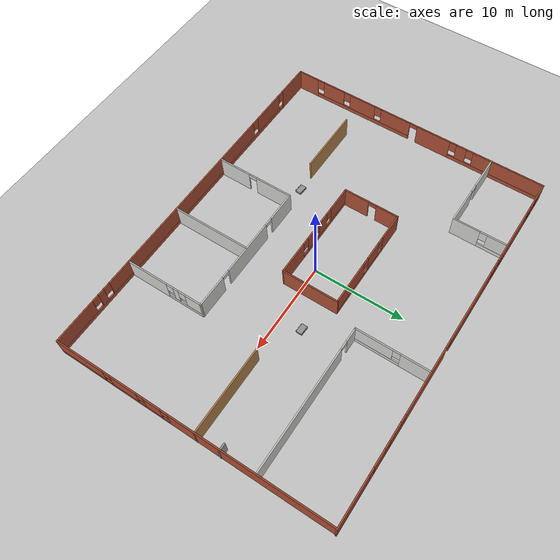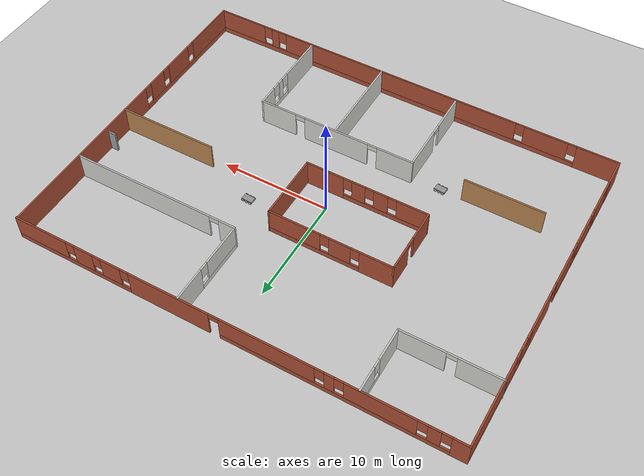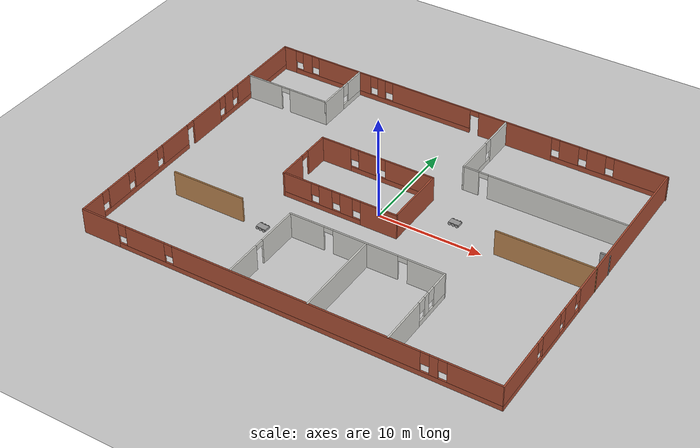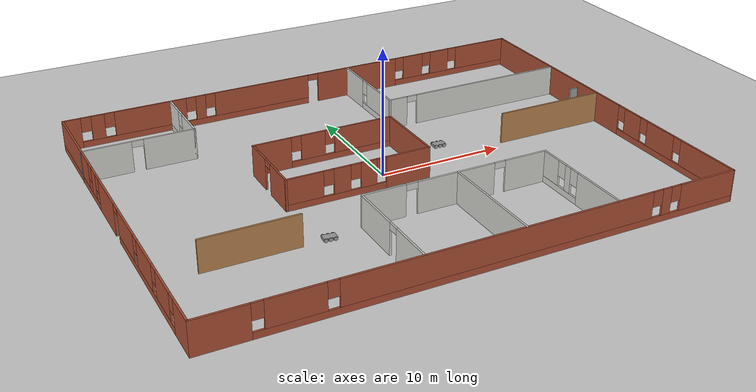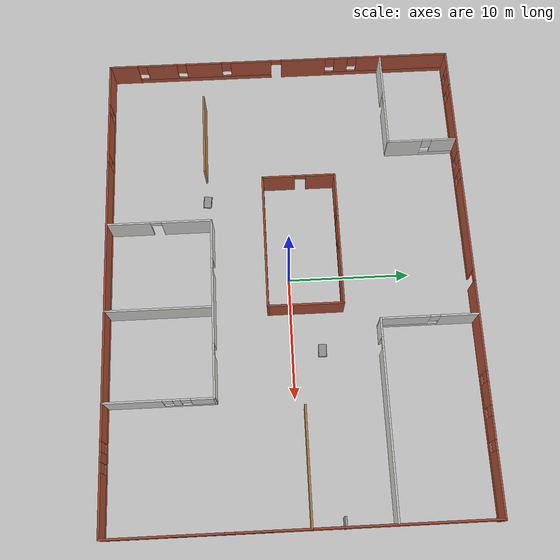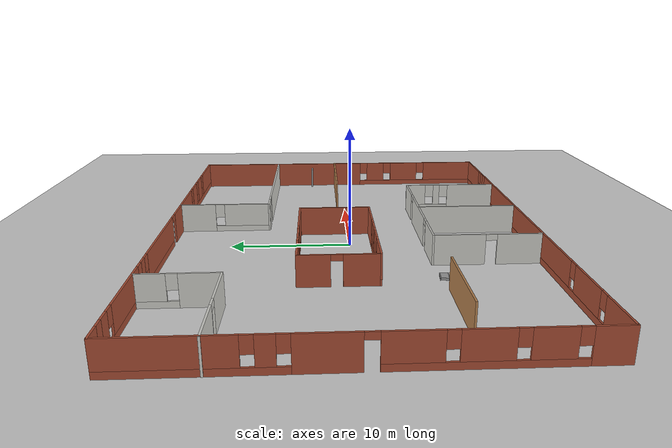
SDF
<sdf version="1.6">
 <world name="default">
  <plugin name="welcome" filename="libwelcome.so"/>
  <light name="sun" type="directional">
   <pose>0 0 10 0 -0 0</pose>
   <diffuse>0.8 0.8 0.8 1</diffuse>
   <specular>0.2 0.2 0.2 1</specular>
   <attenuation>
    <range>1000</range>
    <constant>0.9</constant>
    <linear>0.01</linear>
    <quadratic>0.001</quadratic>
   </attenuation>
   <direction>-0.5 0.1 -0.9</direction>
  </light>
  <model name="ground_plane">
   <static>1</static>
   <link name="link">
    <collision name="collision">
     <geometry><plane><normal>0 0 1</normal><size>100 100</size></plane></geometry>
     <surface>
      <contact><collide_bitmask>65535</collide_bitmask></contact>
      <friction><ode><mu>100</mu><mu2>50</mu2></ode></friction>
     </surface>
    </collision>
    <visual name="visual">
     <cast_shadows>0</cast_shadows>
     <geometry><plane><normal>0 0 1</normal><size>100 100</size></plane></geometry>
     <material>
      <script><uri>file://media/materials/scripts/gazebo.material</uri><name>Gazebo/Grey</name></script>
     </material>
    </visual>
   </link>
  </model>
  <gravity>0 0 -9.8</gravity>
  <magnetic_field>6e-06 2.3e-05 -4.2e-05</magnetic_field>
  <atmosphere type="adiabatic"/>
  <physics name="default_physics" default="0" type="ode">
   <max_step_size>0.001</max_step_size>
   <real_time_factor>1</real_time_factor>
   <real_time_update_rate>1000</real_time_update_rate>
  </physics>
  <scene><ambient>0.4 0.4 0.4 1</ambient><background>0.7 0.7 0.7 1</background><shadows>1</shadows></scene>
  <audio><device>default</device></audio>
  <spherical_coordinates>
   <surface_model>EARTH_WGS84</surface_model>
   <latitude_deg>0</latitude_deg>
   <longitude_deg>0</longitude_deg>
   <elevation>0</elevation>
   <heading_deg>0</heading_deg>
  </spherical_coordinates>
  <model name="Office2">
   <pose>0.0583 0.03565 0 0 -0 0</pose>
   <link name="Door_3">
    <collision name="Door_3_Collision">
     <geometry><box><size>0.9 0.17 2</size></box></geometry>
     <pose>0 0 1 0 -0 0</pose>
    </collision>
    <visual name="Door_3_Visual">
     <pose>0 0 1 0 -0 0</pose>
     <geometry><box><size>0.9 0.17 2</size></box></geometry>
     <material>
      <script><uri>file://media/materials/scripts/gazebo.material</uri><name>Gazebo/Grey</name></script>
     </material>
    </visual>
    <pose>19.6108 3.24042 0 0 -0 0</pose>
   </link>
   <link name="Wall_0">
    <pose>-19.9784 0.000161 0 0 -0 1.5708</pose>
    <visual name="Wall_0_Visual_0">
     <pose>-13.757 0 1.25 0 -0 0</pose>
     <geometry><box><size>2.48598 0.15 2.5</size></box></geometry>
     <material>
      <script><uri>file://media/materials/scripts/gazebo.material</uri><name>Gazebo/Bricks</name></script>
      <ambient>1 1 1 1</ambient>
     </material>
     <meta><layer>0</layer></meta>
    </visual>
    <collision name="Wall_0_Collision_0">
     <geometry><box><size>2.48598 0.15 2.5</size></box></geometry>
     <pose>-13.757 0 1.25 0 -0 0</pose>
    </collision>
    <visual name="Wall_0_Visual_1">
     <pose>2.2039 0 1.25 0 -0 0</pose>
     <geometry><box><size>3.96148 0.15 2.5</size></box></geometry>
     <material>
      <script><uri>file://media/materials/scripts/gazebo.material</uri><name>Gazebo/Bricks</name></script>
      <ambient>1 1 1 1</ambient>
     </material>
     <meta><layer>0</layer></meta>
    </visual>
    <collision name="Wall_0_Collision_1">
     <geometry><box><size>3.96148 0.15 2.5</size></box></geometry>
     <pose>2.2039 0 1.25 0 -0 0</pose>
    </collision>
    <visual name="Wall_0_Visual_2">
     <pose>-6.59543 0 0.25 0 -0 0</pose>
     <geometry><box><size>11.8372 0.15 0.5</size></box></geometry>
     <material>
      <script><uri>file://media/materials/scripts/gazebo.material</uri><name>Gazebo/Bricks</name></script>
      <ambient>1 1 1 1</ambient>
     </material>
     <meta><layer>0</layer></meta>
    </visual>
    <collision name="Wall_0_Collision_2">
     <geometry><box><size>11.8372 0.15 0.5</size></box></geometry>
     <pose>-6.59543 0 0.25 0 -0 0</pose>
    </collision>
    <visual name="Wall_0_Visual_3">
     <pose>9.59232 0 0.25 0 -0 0</pose>
     <geometry><box><size>10.8154 0.15 0.5</size></box></geometry>
     <material>
      <script><uri>file://media/materials/scripts/gazebo.material</uri><name>Gazebo/Bricks</name></script>
      <ambient>1 1 1 1</ambient>
     </material>
     <meta><layer>0</layer></meta>
    </visual>
    <collision name="Wall_0_Collision_3">
     <geometry><box><size>10.8154 0.15 0.5</size></box></geometry>
     <pose>9.59232 0 0.25 0 -0 0</pose>
    </collision>
    <visual name="Wall_0_Visual_4">
     <pose>-10.3805 0 1.5 0 -0 0</pose>
     <geometry><box><size>2.6671 0.15 2</size></box></geometry>
     <material>
      <script><uri>file://media/materials/scripts/gazebo.material</uri><name>Gazebo/Bricks</name></script>
      <ambient>1 1 1 1</ambient>
     </material>
     <meta><layer>0</layer></meta>
    </visual>
    <collision name="Wall_0_Collision_4">
     <geometry><box><size>2.6671 0.15 2</size></box></geometry>
     <pose>-10.3805 0 1.5 0 -0 0</pose>
    </collision>
    <visual name="Wall_0_Visual_5">
     <pose>-6.66573 0 1.5 0 -0 0</pose>
     <geometry><box><size>3.1624 0.15 2</size></box></geometry>
     <material>
      <script><uri>file://media/materials/scripts/gazebo.material</uri><name>Gazebo/Bricks</name></script>
      <ambient>1 1 1 1</ambient>
     </material>
     <meta><layer>0</layer></meta>
    </visual>
    <collision name="Wall_0_Collision_5">
     <geometry><box><size>3.1624 0.15 2</size></box></geometry>
     <pose>-6.66573 0 1.5 0 -0 0</pose>
    </collision>
    <visual name="Wall_0_Visual_6">
     <pose>-2.48068 0 1.5 0 -0 0</pose>
     <geometry><box><size>3.6077 0.15 2</size></box></geometry>
     <material>
      <script><uri>file://media/materials/scripts/gazebo.material</uri><name>Gazebo/Bricks</name></script>
      <ambient>1 1 1 1</ambient>
     </material>
     <meta><layer>0</layer></meta>
    </visual>
    <collision name="Wall_0_Collision_6">
     <geometry><box><size>3.6077 0.15 2</size></box></geometry>
     <pose>-2.48068 0 1.5 0 -0 0</pose>
    </collision>
    <visual name="Wall_0_Visual_7">
     <pose>-2.48068 0 1.5 0 -0 0</pose>
     <geometry><box><size>3.6077 0.15 2</size></box></geometry>
     <material>
      <script><uri>file://media/materials/scripts/gazebo.material</uri><name>Gazebo/Bricks</name></script>
      <ambient>1 1 1 1</ambient>
     </material>
     <meta><layer>0</layer></meta>
    </visual>
    <collision name="Wall_0_Collision_7">
     <geometry><box><size>3.6077 0.15 2</size></box></geometry>
     <pose>-2.48068 0 1.5 0 -0 0</pose>
    </collision>
    <visual name="Wall_0_Visual_8">
     <pose>5.57524 0 1.5 0 -0 0</pose>
     <geometry><box><size>1.1812 0.15 2</size></box></geometry>
     <material>
      <script><uri>file://media/materials/scripts/gazebo.material</uri><name>Gazebo/Bricks</name></script>
      <ambient>1 1 1 1</ambient>
     </material>
     <meta><layer>0</layer></meta>
    </visual>
    <collision name="Wall_0_Collision_8">
     <geometry><box><size>1.1812 0.15 2</size></box></geometry>
     <pose>5.57524 0 1.5 0 -0 0</pose>
    </collision>
    <visual name="Wall_0_Visual_9">
     <pose>10.9829 0 1.5 0 -0 0</pose>
     <geometry><box><size>8.03416 0.15 2</size></box></geometry>
     <material>
      <script><uri>file://media/materials/scripts/gazebo.material</uri><name>Gazebo/Bricks</name></script>
      <ambient>1 1 1 1</ambient>
     </material>
     <meta><layer>0</layer></meta>
    </visual>
    <collision name="Wall_0_Collision_9">
     <geometry><box><size>8.03416 0.15 2</size></box></geometry>
     <pose>10.9829 0 1.5 0 -0 0</pose>
    </collision>
    <visual name="Wall_0_Visual_10">
     <pose>-12.114 0 1.9 0 -0 0</pose>
     <geometry><box><size>0.8 0.15 1.2</size></box></geometry>
     <material>
      <script><uri>file://media/materials/scripts/gazebo.material</uri><name>Gazebo/Bricks</name></script>
      <ambient>1 1 1 1</ambient>
     </material>
     <meta><layer>0</layer></meta>
    </visual>
    <collision name="Wall_0_Collision_10">
     <geometry><box><size>0.8 0.15 1.2</size></box></geometry>
     <pose>-12.114 0 1.9 0 -0 0</pose>
    </collision>
    <visual name="Wall_0_Visual_11">
     <pose>4.58464 0 1.9 0 -0 0</pose>
     <geometry><box><size>0.8 0.15 1.2</size></box></geometry>
     <material>
      <script><uri>file://media/materials/scripts/gazebo.material</uri><name>Gazebo/Bricks</name></script>
      <ambient>1 1 1 1</ambient>
     </material>
     <meta><layer>0</layer></meta>
    </visual>
    <collision name="Wall_0_Collision_11">
     <geometry><box><size>0.8 0.15 1.2</size></box></geometry>
     <pose>4.58464 0 1.9 0 -0 0</pose>
    </collision>
    <visual name="Wall_0_Visual_12">
     <pose>-8.64693 0 1.9 0 -0 0</pose>
     <geometry><box><size>0.8 0.15 1.2</size></box></geometry>
     <material>
      <script><uri>file://media/materials/scripts/gazebo.material</uri><name>Gazebo/Bricks</name></script>
      <ambient>1 1 1 1</ambient>
     </material>
     <meta><layer>0</layer></meta>
    </visual>
    <collision name="Wall_0_Collision_12">
     <geometry><box><size>0.8 0.15 1.2</size></box></geometry>
     <pose>-8.64693 0 1.9 0 -0 0</pose>
    </collision>
    <visual name="Wall_0_Visual_13">
     <pose>-4.68453 0 1.9 0 -0 0</pose>
     <geometry><box><size>0.8 0.15 1.2</size></box></geometry>
     <material>
      <script><uri>file://media/materials/scripts/gazebo.material</uri><name>Gazebo/Bricks</name></script>
      <ambient>1 1 1 1</ambient>
     </material>
     <meta><layer>0</layer></meta>
    </visual>
    <collision name="Wall_0_Collision_13">
     <geometry><box><size>0.8 0.15 1.2</size></box></geometry>
     <pose>-4.68453 0 1.9 0 -0 0</pose>
    </collision>
    <visual name="Wall_0_Visual_14">
     <pose>6.56584 0 1.9 0 -0 0</pose>
     <geometry><box><size>0.8 0.15 1.2</size></box></geometry>
     <material>
      <script><uri>file://media/materials/scripts/gazebo.material</uri><name>Gazebo/Bricks</name></script>
      <ambient>1 1 1 1</ambient>
     </material>
     <meta><layer>0</layer></meta>
    </visual>
    <collision name="Wall_0_Collision_14">
     <geometry><box><size>0.8 0.15 1.2</size></box></geometry>
     <pose>6.56584 0 1.9 0 -0 0</pose>
    </collision>
    <visual name="Wall_0_Visual_15">
     <pose>-0.226838 0 2.25 0 -0 0</pose>
     <geometry><box><size>0.9 0.15 0.5</size></box></geometry>
     <material>
      <script><uri>file://media/materials/scripts/gazebo.material</uri><name>Gazebo/Bricks</name></script>
      <ambient>1 1 1 1</ambient>
     </material>
     <meta><layer>0</layer></meta>
    </visual>
    <collision name="Wall_0_Collision_15">
     <geometry><box><size>0.9 0.15 0.5</size></box></geometry>
     <pose>-0.226838 0 2.25 0 -0 0</pose>
    </collision>
    <visual name="Wall_0_Visual_16">
     <pose>-0.226838 0 2.25 0 -0 0</pose>
     <geometry><box><size>0.9 0.15 0.5</size></box></geometry>
     <material>
      <script><uri>file://media/materials/scripts/gazebo.material</uri><name>Gazebo/Bricks</name></script>
      <ambient>1 1 1 1</ambient>
     </material>
     <meta><layer>0</layer></meta>
    </visual>
    <collision name="Wall_0_Collision_16">
     <geometry><box><size>0.9 0.15 0.5</size></box></geometry>
     <pose>-0.226838 0 2.25 0 -0 0</pose>
    </collision>
   </link>
   <link name="Wall_11">
    <pose>-15.7131 9.0425 0 0 -0 0</pose>
    <visual name="Wall_11_Visual_0">
     <pose>-2.47517 0 1.25 0 -0 0</pose>
     <geometry><box><size>3.79967 0.15 2.5</size></box></geometry>
     <material>
      <script><uri>file://media/materials/scripts/gazebo.material</uri><name>Gazebo/CeilingTiled</name></script>
      <ambient>0.203922 0.396078 0.643137 1</ambient>
     </material>
     <meta><layer>0</layer></meta>
    </visual>
    <collision name="Wall_11_Collision_0">
     <geometry><box><size>3.79967 0.15 2.5</size></box></geometry>
     <pose>-2.47517 0 1.25 0 -0 0</pose>
    </collision>
    <visual name="Wall_11_Visual_1">
     <pose>2.34983 0 1.25 0 -0 0</pose>
     <geometry><box><size>4.05033 0.15 2.5</size></box></geometry>
     <material>
      <script><uri>file://media/materials/scripts/gazebo.material</uri><name>Gazebo/CeilingTiled</name></script>
      <ambient>0.203922 0.396078 0.643137 1</ambient>
     </material>
     <meta><layer>0</layer></meta>
    </visual>
    <collision name="Wall_11_Collision_1">
     <geometry><box><size>4.05033 0.15 2.5</size></box></geometry>
     <pose>2.34983 0 1.25 0 -0 0</pose>
    </collision>
    <visual name="Wall_11_Visual_2">
     <pose>-0.125334 0 2.25 0 -0 0</pose>
     <geometry><box><size>0.9 0.15 0.5</size></box></geometry>
     <material>
      <script><uri>file://media/materials/scripts/gazebo.material</uri><name>Gazebo/CeilingTiled</name></script>
      <ambient>0.203922 0.396078 0.643137 1</ambient>
     </material>
     <meta><layer>0</layer></meta>
    </visual>
    <collision name="Wall_11_Collision_2">
     <geometry><box><size>0.9 0.15 0.5</size></box></geometry>
     <pose>-0.125334 0 2.25 0 -0 0</pose>
    </collision>
   </link>
   <link name="Wall_15">
    <pose>-11.4131 11.9675 0 0 -0 1.5708</pose>
    <visual name="Wall_15_Visual_0">
     <pose>-1.49971 0 1.25 0 -0 0</pose>
     <geometry><box><size>3.00058 0.15 2.5</size></box></geometry>
     <material>
      <script><uri>file://media/materials/scripts/gazebo.material</uri><name>Gazebo/CeilingTiled</name></script>
      <ambient>1 1 1 1</ambient>
     </material>
     <meta><layer>0</layer></meta>
    </visual>
    <collision name="Wall_15_Collision_0">
     <geometry><box><size>3.00058 0.15 2.5</size></box></geometry>
     <pose>-1.49971 0 1.25 0 -0 0</pose>
    </collision>
    <visual name="Wall_15_Visual_1">
     <pose>1.50029 0 0.25 0 -0 0</pose>
     <geometry><box><size>2.99942 0.15 0.5</size></box></geometry>
     <material>
      <script><uri>file://media/materials/scripts/gazebo.material</uri><name>Gazebo/CeilingTiled</name></script>
      <ambient>1 1 1 1</ambient>
     </material>
     <meta><layer>0</layer></meta>
    </visual>
    <collision name="Wall_15_Collision_1">
     <geometry><box><size>2.99942 0.15 0.5</size></box></geometry>
     <pose>1.50029 0 0.25 0 -0 0</pose>
    </collision>
    <visual name="Wall_15_Visual_2">
     <pose>1.90029 0 1.5 0 -0 0</pose>
     <geometry><box><size>2.19942 0.15 2</size></box></geometry>
     <material>
      <script><uri>file://media/materials/scripts/gazebo.material</uri><name>Gazebo/CeilingTiled</name></script>
      <ambient>1 1 1 1</ambient>
     </material>
     <meta><layer>0</layer></meta>
    </visual>
    <collision name="Wall_15_Collision_2">
     <geometry><box><size>2.19942 0.15 2</size></box></geometry>
     <pose>1.90029 0 1.5 0 -0 0</pose>
    </collision>
    <visual name="Wall_15_Visual_3">
     <pose>0.400581 0 1.9 0 -0 0</pose>
     <geometry><box><size>0.8 0.15 1.2</size></box></geometry>
     <material>
      <script><uri>file://media/materials/scripts/gazebo.material</uri><name>Gazebo/CeilingTiled</name></script>
      <ambient>1 1 1 1</ambient>
     </material>
     <meta><layer>0</layer></meta>
    </visual>
    <collision name="Wall_15_Collision_3">
     <geometry><box><size>0.8 0.15 1.2</size></box></geometry>
     <pose>0.400581 0 1.9 0 -0 0</pose>
    </collision>
   </link>
   <link name="Wall_17">
    <pose>4.25654 10.9903 0 0 -0 -1.5708</pose>
    <visual name="Wall_17_Visual_0">
     <pose>-2.42895 0 1.25 0 -0 0</pose>
     <geometry><box><size>3.1421 0.15 2.5</size></box></geometry>
     <material>
      <script><uri>file://media/materials/scripts/gazebo.material</uri><name>Gazebo/CeilingTiled</name></script>
      <ambient>1 1 1 1</ambient>
     </material>
     <meta><layer>0</layer></meta>
    </visual>
    <collision name="Wall_17_Collision_0">
     <geometry><box><size>3.1421 0.15 2.5</size></box></geometry>
     <pose>-2.42895 0 1.25 0 -0 0</pose>
    </collision>
    <visual name="Wall_17_Visual_1">
     <pose>1.57105 0 0.25 0 -0 0</pose>
     <geometry><box><size>4.8579 0.15 0.5</size></box></geometry>
     <material>
      <script><uri>file://media/materials/scripts/gazebo.material</uri><name>Gazebo/CeilingTiled</name></script>
      <ambient>1 1 1 1</ambient>
     </material>
     <meta><layer>0</layer></meta>
    </visual>
    <collision name="Wall_17_Collision_1">
     <geometry><box><size>4.8579 0.15 0.5</size></box></geometry>
     <pose>1.57105 0 0.25 0 -0 0</pose>
    </collision>
    <visual name="Wall_17_Visual_2">
     <pose>1.97105 0 1.5 0 -0 0</pose>
     <geometry><box><size>4.0579 0.15 2</size></box></geometry>
     <material>
      <script><uri>file://media/materials/scripts/gazebo.material</uri><name>Gazebo/CeilingTiled</name></script>
      <ambient>1 1 1 1</ambient>
     </material>
     <meta><layer>0</layer></meta>
    </visual>
    <collision name="Wall_17_Collision_2">
     <geometry><box><size>4.0579 0.15 2</size></box></geometry>
     <pose>1.97105 0 1.5 0 -0 0</pose>
    </collision>
    <visual name="Wall_17_Visual_3">
     <pose>-0.457904 0 1.9 0 -0 0</pose>
     <geometry><box><size>0.8 0.15 1.2</size></box></geometry>
     <material>
      <script><uri>file://media/materials/scripts/gazebo.material</uri><name>Gazebo/CeilingTiled</name></script>
      <ambient>1 1 1 1</ambient>
     </material>
     <meta><layer>0</layer></meta>
    </visual>
    <collision name="Wall_17_Collision_3">
     <geometry><box><size>0.8 0.15 1.2</size></box></geometry>
     <pose>-0.457904 0 1.9 0 -0 0</pose>
    </collision>
   </link>
   <link name="Wall_18">
    <pose>12.0565 7.06533 0 0 -0 0</pose>
    <visual name="Wall_18_Visual_0">
     <pose>-7.0719 0 1.25 0 -0 0</pose>
     <geometry><box><size>1.6062 0.15 2.5</size></box></geometry>
     <material>
      <script><uri>file://media/materials/scripts/gazebo.material</uri><name>Gazebo/CeilingTiled</name></script>
      <ambient>0.203922 0.396078 0.643137 1</ambient>
     </material>
     <meta><layer>0</layer></meta>
    </visual>
    <collision name="Wall_18_Collision_0">
     <geometry><box><size>1.6062 0.15 2.5</size></box></geometry>
     <pose>-7.0719 0 1.25 0 -0 0</pose>
    </collision>
    <visual name="Wall_18_Visual_1">
     <pose>1.2531 0 1.25 0 -0 0</pose>
     <geometry><box><size>13.2438 0.15 2.5</size></box></geometry>
     <material>
      <script><uri>file://media/materials/scripts/gazebo.material</uri><name>Gazebo/CeilingTiled</name></script>
      <ambient>0.203922 0.396078 0.643137 1</ambient>
     </material>
     <meta><layer>0</layer></meta>
    </visual>
    <collision name="Wall_18_Collision_1">
     <geometry><box><size>13.2438 0.15 2.5</size></box></geometry>
     <pose>1.2531 0 1.25 0 -0 0</pose>
    </collision>
    <visual name="Wall_18_Visual_2">
     <pose>-5.8188 0 2.25 0 -0 0</pose>
     <geometry><box><size>0.9 0.15 0.5</size></box></geometry>
     <material>
      <script><uri>file://media/materials/scripts/gazebo.material</uri><name>Gazebo/CeilingTiled</name></script>
      <ambient>0.203922 0.396078 0.643137 1</ambient>
     </material>
     <meta><layer>0</layer></meta>
    </visual>
    <collision name="Wall_18_Collision_2">
     <geometry><box><size>0.9 0.15 0.5</size></box></geometry>
     <pose>-5.8188 0 2.25 0 -0 0</pose>
    </collision>
   </link>
   <link name="Wall_20">
    <pose>9.98786 -10.5734 0 0 -0 1.5708</pose>
    <visual name="Wall_20_Visual_0">
     <pose>-2.061 0 1.25 0 -0 0</pose>
     <geometry><box><size>4.62799 0.15 2.5</size></box></geometry>
     <material>
      <script><uri>file://media/materials/scripts/gazebo.material</uri><name>Gazebo/CeilingTiled</name></script>
      <ambient>1 1 1 1</ambient>
     </material>
     <meta><layer>0</layer></meta>
    </visual>
    <collision name="Wall_20_Collision_0">
     <geometry><box><size>4.62799 0.15 2.5</size></box></geometry>
     <pose>-2.061 0 1.25 0 -0 0</pose>
    </collision>
    <visual name="Wall_20_Visual_1">
     <pose>2.314 0 0.25 0 -0 0</pose>
     <geometry><box><size>4.12201 0.15 0.5</size></box></geometry>
     <material>
      <script><uri>file://media/materials/scripts/gazebo.material</uri><name>Gazebo/CeilingTiled</name></script>
      <ambient>1 1 1 1</ambient>
     </material>
     <meta><layer>0</layer></meta>
    </visual>
    <collision name="Wall_20_Collision_1">
     <geometry><box><size>4.12201 0.15 0.5</size></box></geometry>
     <pose>2.314 0 0.25 0 -0 0</pose>
    </collision>
    <visual name="Wall_20_Visual_2">
     <pose>1.36057 0 1.5 0 -0 0</pose>
     <geometry><box><size>0.615141 0.15 2</size></box></geometry>
     <material>
      <script><uri>file://media/materials/scripts/gazebo.material</uri><name>Gazebo/CeilingTiled</name></script>
      <ambient>1 1 1 1</ambient>
     </material>
     <meta><layer>0</layer></meta>
    </visual>
    <collision name="Wall_20_Collision_2">
     <geometry><box><size>0.615141 0.15 2</size></box></geometry>
     <pose>1.36057 0 1.5 0 -0 0</pose>
    </collision>
    <visual name="Wall_20_Visual_3">
     <pose>3.42157 0 1.5 0 -0 0</pose>
     <geometry><box><size>1.90687 0.15 2</size></box></geometry>
     <material>
      <script><uri>file://media/materials/scripts/gazebo.material</uri><name>Gazebo/CeilingTiled</name></script>
      <ambient>1 1 1 1</ambient>
     </material>
     <meta><layer>0</layer></meta>
    </visual>
    <collision name="Wall_20_Collision_3">
     <geometry><box><size>1.90687 0.15 2</size></box></geometry>
     <pose>3.42157 0 1.5 0 -0 0</pose>
    </collision>
    <visual name="Wall_20_Visual_4">
     <pose>0.652994 0 1.9 0 -0 0</pose>
     <geometry><box><size>0.8 0.15 1.2</size></box></geometry>
     <material>
      <script><uri>file://media/materials/scripts/gazebo.material</uri><name>Gazebo/CeilingTiled</name></script>
      <ambient>1 1 1 1</ambient>
     </material>
     <meta><layer>0</layer></meta>
    </visual>
    <collision name="Wall_20_Collision_4">
     <geometry><box><size>0.8 0.15 1.2</size></box></geometry>
     <pose>0.652994 0 1.9 0 -0 0</pose>
    </collision>
    <visual name="Wall_20_Visual_5">
     <pose>2.06813 0 1.9 0 -0 0</pose>
     <geometry><box><size>0.8 0.15 1.2</size></box></geometry>
     <material>
      <script><uri>file://media/materials/scripts/gazebo.material</uri><name>Gazebo/CeilingTiled</name></script>
      <ambient>1 1 1 1</ambient>
     </material>
     <meta><layer>0</layer></meta>
    </visual>
    <collision name="Wall_20_Collision_5">
     <geometry><box><size>0.8 0.15 1.2</size></box></geometry>
     <pose>2.06813 0 1.9 0 -0 0</pose>
    </collision>
   </link>
   <link name="Wall_21">
    <pose>2.56286 -6.27339 0 0 -0 3.14159</pose>
    <visual name="Wall_21_Visual_0">
     <pose>-5.74168 0 1.25 0 -0 0</pose>
     <geometry><box><size>3.51664 0.15 2.5</size></box></geometry>
     <material>
      <script><uri>file://media/materials/scripts/gazebo.material</uri><name>Gazebo/CeilingTiled</name></script>
      <ambient>0.203922 0.396078 0.643137 1</ambient>
     </material>
     <meta><layer>0</layer></meta>
    </visual>
    <collision name="Wall_21_Collision_0">
     <geometry><box><size>3.51664 0.15 2.5</size></box></geometry>
     <pose>-5.74168 0 1.25 0 -0 0</pose>
    </collision>
    <visual name="Wall_21_Visual_1">
     <pose>0.03987 0 1.25 0 -0 0</pose>
     <geometry><box><size>6.24646 0.15 2.5</size></box></geometry>
     <material>
      <script><uri>file://media/materials/scripts/gazebo.material</uri><name>Gazebo/CeilingTiled</name></script>
      <ambient>0.203922 0.396078 0.643137 1</ambient>
     </material>
     <meta><layer>0</layer></meta>
    </visual>
    <collision name="Wall_21_Collision_1">
     <geometry><box><size>6.24646 0.15 2.5</size></box></geometry>
     <pose>0.03987 0 1.25 0 -0 0</pose>
    </collision>
    <visual name="Wall_21_Visual_2">
     <pose>5.78155 0 1.25 0 -0 0</pose>
     <geometry><box><size>3.4369 0.15 2.5</size></box></geometry>
     <material>
      <script><uri>file://media/materials/scripts/gazebo.material</uri><name>Gazebo/CeilingTiled</name></script>
      <ambient>0.203922 0.396078 0.643137 1</ambient>
     </material>
     <meta><layer>0</layer></meta>
    </visual>
    <collision name="Wall_21_Collision_2">
     <geometry><box><size>3.4369 0.15 2.5</size></box></geometry>
     <pose>5.78155 0 1.25 0 -0 0</pose>
    </collision>
    <visual name="Wall_21_Visual_3">
     <pose>-3.53336 0 2.25 0 -0 0</pose>
     <geometry><box><size>0.9 0.15 0.5</size></box></geometry>
     <material>
      <script><uri>file://media/materials/scripts/gazebo.material</uri><name>Gazebo/CeilingTiled</name></script>
      <ambient>0.203922 0.396078 0.643137 1</ambient>
     </material>
     <meta><layer>0</layer></meta>
    </visual>
    <collision name="Wall_21_Collision_3">
     <geometry><box><size>0.9 0.15 0.5</size></box></geometry>
     <pose>-3.53336 0 2.25 0 -0 0</pose>
    </collision>
    <visual name="Wall_21_Visual_4">
     <pose>3.6131 0 2.25 0 -0 0</pose>
     <geometry><box><size>0.9 0.15 0.5</size></box></geometry>
     <material>
      <script><uri>file://media/materials/scripts/gazebo.material</uri><name>Gazebo/CeilingTiled</name></script>
      <ambient>0.203922 0.396078 0.643137 1</ambient>
     </material>
     <meta><layer>0</layer></meta>
    </visual>
    <collision name="Wall_21_Collision_4">
     <geometry><box><size>0.9 0.15 0.5</size></box></geometry>
     <pose>3.6131 0 2.25 0 -0 0</pose>
    </collision>
   </link>
   <link name="Wall_22">
    <pose>-4.86214 -10.5734 0 0 -0 -1.5708</pose>
    <visual name="Wall_22_Visual_0">
     <pose>-2.27908 0 1.25 0 -0 0</pose>
     <geometry><box><size>4.19185 0.15 2.5</size></box></geometry>
     <material>
      <script><uri>file://media/materials/scripts/gazebo.material</uri><name>Gazebo/CeilingTiled</name></script>
      <ambient>1 1 1 1</ambient>
     </material>
     <meta><layer>0</layer></meta>
    </visual>
    <collision name="Wall_22_Collision_0">
     <geometry><box><size>4.19185 0.15 2.5</size></box></geometry>
     <pose>-2.27908 0 1.25 0 -0 0</pose>
    </collision>
    <visual name="Wall_22_Visual_1">
     <pose>2.54592 0 1.25 0 -0 0</pose>
     <geometry><box><size>3.65815 0.15 2.5</size></box></geometry>
     <material>
      <script><uri>file://media/materials/scripts/gazebo.material</uri><name>Gazebo/CeilingTiled</name></script>
      <ambient>1 1 1 1</ambient>
     </material>
     <meta><layer>0</layer></meta>
    </visual>
    <collision name="Wall_22_Collision_1">
     <geometry><box><size>3.65815 0.15 2.5</size></box></geometry>
     <pose>2.54592 0 1.25 0 -0 0</pose>
    </collision>
    <visual name="Wall_22_Visual_2">
     <pose>0.266848 0 2.25 0 -0 0</pose>
     <geometry><box><size>0.9 0.15 0.5</size></box></geometry>
     <material>
      <script><uri>file://media/materials/scripts/gazebo.material</uri><name>Gazebo/CeilingTiled</name></script>
      <ambient>1 1 1 1</ambient>
     </material>
     <meta><layer>0</layer></meta>
    </visual>
    <collision name="Wall_22_Collision_2">
     <geometry><box><size>0.9 0.15 0.5</size></box></geometry>
     <pose>0.266848 0 2.25 0 -0 0</pose>
    </collision>
   </link>
   <link name="Wall_24">
    <collision name="Wall_24_Collision">
     <geometry><box><size>8.75 0.15 2.5</size></box></geometry>
     <pose>0 0 1.25 0 -0 0</pose>
    </collision>
    <visual name="Wall_24_Visual">
     <pose>0 0 1.25 0 -0 0</pose>
     <geometry><box><size>8.75 0.15 2.5</size></box></geometry>
     <material>
      <script><uri>file://media/materials/scripts/gazebo.material</uri><name>Gazebo/CeilingTiled</name></script>
      <ambient>1 1 1 1</ambient>
     </material>
     <meta><layer>0</layer></meta>
    </visual>
    <pose>2.62913 -10.6118 0 0 -0 -1.5708</pose>
   </link>
   <link name="Wall_26">
    <pose>-2.87549 4.23102 0 0 -0 0</pose>
    <visual name="Wall_26_Visual_0">
     <pose>-4.21433 0 1.25 0 -0 0</pose>
     <geometry><box><size>3.07134 0.15 2.5</size></box></geometry>
     <material>
      <script><uri>file://media/materials/scripts/gazebo.material</uri><name>Gazebo/Bricks</name></script>
      <ambient>1 1 1 1</ambient>
     </material>
     <meta><layer>0</layer></meta>
    </visual>
    <collision name="Wall_26_Collision_0">
     <geometry><box><size>3.07134 0.15 2.5</size></box></geometry>
     <pose>-4.21433 0 1.25 0 -0 0</pose>
    </collision>
    <visual name="Wall_26_Visual_1">
     <pose>1.53567 0 0.25 0 -0 0</pose>
     <geometry><box><size>8.42866 0.15 0.5</size></box></geometry>
     <material>
      <script><uri>file://media/materials/scripts/gazebo.material</uri><name>Gazebo/Bricks</name></script>
      <ambient>1 1 1 1</ambient>
     </material>
     <meta><layer>0</layer></meta>
    </visual>
    <collision name="Wall_26_Collision_1">
     <geometry><box><size>8.42866 0.15 0.5</size></box></geometry>
     <pose>1.53567 0 0.25 0 -0 0</pose>
    </collision>
    <visual name="Wall_26_Visual_2">
     <pose>-0.898898 0 1.5 0 -0 0</pose>
     <geometry><box><size>1.95952 0.15 2</size></box></geometry>
     <material>
      <script><uri>file://media/materials/scripts/gazebo.material</uri><name>Gazebo/Bricks</name></script>
      <ambient>1 1 1 1</ambient>
     </material>
     <meta><layer>0</layer></meta>
    </visual>
    <collision name="Wall_26_Collision_2">
     <geometry><box><size>1.95952 0.15 2</size></box></geometry>
     <pose>-0.898898 0 1.5 0 -0 0</pose>
    </collision>
    <visual name="Wall_26_Visual_3">
     <pose>3.31543 0 1.5 0 -0 0</pose>
     <geometry><box><size>4.86913 0.15 2</size></box></geometry>
     <material>
      <script><uri>file://media/materials/scripts/gazebo.material</uri><name>Gazebo/Bricks</name></script>
      <ambient>1 1 1 1</ambient>
     </material>
     <meta><layer>0</layer></meta>
    </visual>
    <collision name="Wall_26_Collision_3">
     <geometry><box><size>4.86913 0.15 2</size></box></geometry>
     <pose>3.31543 0 1.5 0 -0 0</pose>
    </collision>
    <visual name="Wall_26_Visual_4">
     <pose>-2.27866 0 1.9 0 -0 0</pose>
     <geometry><box><size>0.8 0.15 1.2</size></box></geometry>
     <material>
      <script><uri>file://media/materials/scripts/gazebo.material</uri><name>Gazebo/Bricks</name></script>
      <ambient>1 1 1 1</ambient>
     </material>
     <meta><layer>0</layer></meta>
    </visual>
    <collision name="Wall_26_Collision_4">
     <geometry><box><size>0.8 0.15 1.2</size></box></geometry>
     <pose>-2.27866 0 1.9 0 -0 0</pose>
    </collision>
    <visual name="Wall_26_Visual_5">
     <pose>0.480865 0 1.9 0 -0 0</pose>
     <geometry><box><size>0.8 0.15 1.2</size></box></geometry>
     <material>
      <script><uri>file://media/materials/scripts/gazebo.material</uri><name>Gazebo/Bricks</name></script>
      <ambient>1 1 1 1</ambient>
     </material>
     <meta><layer>0</layer></meta>
    </visual>
    <collision name="Wall_26_Collision_5">
     <geometry><box><size>0.8 0.15 1.2</size></box></geometry>
     <pose>0.480865 0 1.9 0 -0 0</pose>
    </collision>
   </link>
   <link name="Wall_27">
    <collision name="Wall_27_Collision">
     <geometry><box><size>6.25 0.15 2.5</size></box></geometry>
     <pose>0 0 1.25 0 -0 0</pose>
    </collision>
    <visual name="Wall_27_Visual">
     <pose>0 0 1.25 0 -0 0</pose>
     <geometry><box><size>6.25 0.15 2.5</size></box></geometry>
     <material>
      <script><uri>file://media/materials/scripts/gazebo.material</uri><name>Gazebo/Bricks</name></script>
      <ambient>1 1 1 1</ambient>
     </material>
     <meta><layer>0</layer></meta>
    </visual>
    <pose>2.79951 1.18102 0 0 -0 -1.5708</pose>
   </link>
   <link name="Wall_28">
    <pose>-2.87549 -1.86898 0 0 -0 3.14159</pose>
    <visual name="Wall_28_Visual_0">
     <pose>-3.95225 0 1.25 0 -0 0</pose>
     <geometry><box><size>3.59551 0.15 2.5</size></box></geometry>
     <material>
      <script><uri>file://media/materials/scripts/gazebo.material</uri><name>Gazebo/Bricks</name></script>
      <ambient>1 1 1 1</ambient>
     </material>
     <meta><layer>0</layer></meta>
    </visual>
    <collision name="Wall_28_Collision_0">
     <geometry><box><size>3.59551 0.15 2.5</size></box></geometry>
     <pose>-3.95225 0 1.25 0 -0 0</pose>
    </collision>
    <visual name="Wall_28_Visual_1">
     <pose>1.79775 0 0.25 0 -0 0</pose>
     <geometry><box><size>7.90449 0.15 0.5</size></box></geometry>
     <material>
      <script><uri>file://media/materials/scripts/gazebo.material</uri><name>Gazebo/Bricks</name></script>
      <ambient>1 1 1 1</ambient>
     </material>
     <meta><layer>0</layer></meta>
    </visual>
    <collision name="Wall_28_Collision_1">
     <geometry><box><size>7.90449 0.15 0.5</size></box></geometry>
     <pose>1.79775 0 0.25 0 -0 0</pose>
    </collision>
    <visual name="Wall_28_Visual_2">
     <pose>-0.728514 0 1.5 0 -0 0</pose>
     <geometry><box><size>1.25195 0.15 2</size></box></geometry>
     <material>
      <script><uri>file://media/materials/scripts/gazebo.material</uri><name>Gazebo/Bricks</name></script>
      <ambient>1 1 1 1</ambient>
     </material>
     <meta><layer>0</layer></meta>
    </visual>
    <collision name="Wall_28_Collision_2">
     <geometry><box><size>1.25195 0.15 2</size></box></geometry>
     <pose>-0.728514 0 1.5 0 -0 0</pose>
    </collision>
    <visual name="Wall_28_Visual_3">
     <pose>1.35882 0 1.5 0 -0 0</pose>
     <geometry><box><size>1.32271 0.15 2</size></box></geometry>
     <material>
      <script><uri>file://media/materials/scripts/gazebo.material</uri><name>Gazebo/Bricks</name></script>
      <ambient>1 1 1 1</ambient>
     </material>
     <meta><layer>0</layer></meta>
    </visual>
    <collision name="Wall_28_Collision_3">
     <geometry><box><size>1.32271 0.15 2</size></box></geometry>
     <pose>1.35882 0 1.5 0 -0 0</pose>
    </collision>
    <visual name="Wall_28_Visual_4">
     <pose>4.28509 0 1.5 0 -0 0</pose>
     <geometry><box><size>2.92983 0.15 2</size></box></geometry>
     <material>
      <script><uri>file://media/materials/scripts/gazebo.material</uri><name>Gazebo/Bricks</name></script>
      <ambient>1 1 1 1</ambient>
     </material>
     <meta><layer>0</layer></meta>
    </visual>
    <collision name="Wall_28_Collision_4">
     <geometry><box><size>2.92983 0.15 2</size></box></geometry>
     <pose>4.28509 0 1.5 0 -0 0</pose>
    </collision>
    <visual name="Wall_28_Visual_5">
     <pose>-1.75449 0 1.9 0 -0 0</pose>
     <geometry><box><size>0.8 0.15 1.2</size></box></geometry>
     <material>
      <script><uri>file://media/materials/scripts/gazebo.material</uri><name>Gazebo/Bricks</name></script>
      <ambient>1 1 1 1</ambient>
     </material>
     <meta><layer>0</layer></meta>
    </visual>
    <collision name="Wall_28_Collision_5">
     <geometry><box><size>0.8 0.15 1.2</size></box></geometry>
     <pose>-1.75449 0 1.9 0 -0 0</pose>
    </collision>
    <visual name="Wall_28_Visual_6">
     <pose>0.297463 0 1.9 0 -0 0</pose>
     <geometry><box><size>0.8 0.15 1.2</size></box></geometry>
     <material>
      <script><uri>file://media/materials/scripts/gazebo.material</uri><name>Gazebo/Bricks</name></script>
      <ambient>1 1 1 1</ambient>
     </material>
     <meta><layer>0</layer></meta>
    </visual>
    <collision name="Wall_28_Collision_6">
     <geometry><box><size>0.8 0.15 1.2</size></box></geometry>
     <pose>0.297463 0 1.9 0 -0 0</pose>
    </collision>
    <visual name="Wall_28_Visual_7">
     <pose>2.42017 0 1.9 0 -0 0</pose>
     <geometry><box><size>0.8 0.15 1.2</size></box></geometry>
     <material>
      <script><uri>file://media/materials/scripts/gazebo.material</uri><name>Gazebo/Bricks</name></script>
      <ambient>1 1 1 1</ambient>
     </material>
     <meta><layer>0</layer></meta>
    </visual>
    <collision name="Wall_28_Collision_7">
     <geometry><box><size>0.8 0.15 1.2</size></box></geometry>
     <pose>2.42017 0 1.9 0 -0 0</pose>
    </collision>
   </link>
   <link name="Wall_29">
    <pose>-8.55049 1.18102 0 0 -0 1.5708</pose>
    <visual name="Wall_29_Visual_0">
     <pose>-1.71302 0 1.25 0 -0 0</pose>
     <geometry><box><size>2.82396 0.15 2.5</size></box></geometry>
     <material>
      <script><uri>file://media/materials/scripts/gazebo.material</uri><name>Gazebo/Bricks</name></script>
      <ambient>1 1 1 1</ambient>
     </material>
     <meta><layer>0</layer></meta>
    </visual>
    <collision name="Wall_29_Collision_0">
     <geometry><box><size>2.82396 0.15 2.5</size></box></geometry>
     <pose>-1.71302 0 1.25 0 -0 0</pose>
    </collision>
    <visual name="Wall_29_Visual_1">
     <pose>1.86198 0 1.25 0 -0 0</pose>
     <geometry><box><size>2.52604 0.15 2.5</size></box></geometry>
     <material>
      <script><uri>file://media/materials/scripts/gazebo.material</uri><name>Gazebo/Bricks</name></script>
      <ambient>1 1 1 1</ambient>
     </material>
     <meta><layer>0</layer></meta>
    </visual>
    <collision name="Wall_29_Collision_1">
     <geometry><box><size>2.52604 0.15 2.5</size></box></geometry>
     <pose>1.86198 0 1.25 0 -0 0</pose>
    </collision>
    <visual name="Wall_29_Visual_2">
     <pose>0.148961 0 2.25 0 -0 0</pose>
     <geometry><box><size>0.9 0.15 0.5</size></box></geometry>
     <material>
      <script><uri>file://media/materials/scripts/gazebo.material</uri><name>Gazebo/Bricks</name></script>
      <ambient>1 1 1 1</ambient>
     </material>
     <meta><layer>0</layer></meta>
    </visual>
    <collision name="Wall_29_Collision_2">
     <geometry><box><size>0.9 0.15 0.5</size></box></geometry>
     <pose>0.148961 0 2.25 0 -0 0</pose>
    </collision>
   </link>
   <link name="Wall_31">
    <collision name="Wall_31_Collision">
     <geometry><box><size>9.25 0.15 2.5</size></box></geometry>
     <pose>0 0 1.25 0 -0 0</pose>
    </collision>
    <visual name="Wall_31_Visual">
     <pose>0 0 1.25 0 -0 0</pose>
     <geometry><box><size>9.25 0.15 2.5</size></box></geometry>
     <material>
      <script><uri>file://media/materials/scripts/gazebo.material</uri><name>Gazebo/Wood</name></script>
      <ambient>1 1 1 1</ambient>
     </material>
     <meta><layer>0</layer></meta>
    </visual>
    <pose>15.4146 0.693165 0 0 -0 3.14159</pose>
   </link>
   <link name="Wall_33">
    <collision name="Wall_33_Collision">
     <geometry><box><size>7.25 0.15 2.5</size></box></geometry>
     <pose>0 0 1.25 0 -0 0</pose>
    </collision>
    <visual name="Wall_33_Visual">
     <pose>0 0 1.25 0 -0 0</pose>
     <geometry><box><size>7.25 0.15 2.5</size></box></geometry>
     <material>
      <script><uri>file://media/materials/scripts/gazebo.material</uri><name>Gazebo/Wood</name></script>
      <ambient>1 1 1 1</ambient>
     </material>
     <meta><layer>0</layer></meta>
    </visual>
    <pose>-13.0668 -6.73633 0 0 -0 0</pose>
   </link>
   <link name="Wall_5">
    <pose>0.017377 14.9252 0 0 -0 0</pose>
    <visual name="Wall_5_Visual_0">
     <pose>-19.3662 0 1.25 0 -0 0</pose>
     <geometry><box><size>1.40917 0.15 2.5</size></box></geometry>
     <material>
      <script><uri>file://media/materials/scripts/gazebo.material</uri><name>Gazebo/Bricks</name></script>
      <ambient>1 1 1 1</ambient>
     </material>
     <meta><layer>0</layer></meta>
    </visual>
    <collision name="Wall_5_Collision_0">
     <geometry><box><size>1.40917 0.15 2.5</size></box></geometry>
     <pose>-19.3662 0 1.25 0 -0 0</pose>
    </collision>
    <visual name="Wall_5_Visual_1">
     <pose>5.14862 0 1.25 0 -0 0</pose>
     <geometry><box><size>7.42858 0.15 2.5</size></box></geometry>
     <material>
      <script><uri>file://media/materials/scripts/gazebo.material</uri><name>Gazebo/Bricks</name></script>
      <ambient>1 1 1 1</ambient>
     </material>
     <meta><layer>0</layer></meta>
    </visual>
    <collision name="Wall_5_Collision_1">
     <geometry><box><size>7.42858 0.15 2.5</size></box></geometry>
     <pose>5.14862 0 1.25 0 -0 0</pose>
    </collision>
    <visual name="Wall_5_Visual_2">
     <pose>-9.06362 0 0.25 0 -0 0</pose>
     <geometry><box><size>19.1959 0.15 0.5</size></box></geometry>
     <material>
      <script><uri>file://media/materials/scripts/gazebo.material</uri><name>Gazebo/Bricks</name></script>
      <ambient>1 1 1 1</ambient>
     </material>
     <meta><layer>0</layer></meta>
    </visual>
    <collision name="Wall_5_Collision_2">
     <geometry><box><size>19.1959 0.15 0.5</size></box></geometry>
     <pose>-9.06362 0 0.25 0 -0 0</pose>
    </collision>
    <visual name="Wall_5_Visual_3">
     <pose>14.4668 0 0.25 0 -0 0</pose>
     <geometry><box><size>11.2078 0.15 0.5</size></box></geometry>
     <material>
      <script><uri>file://media/materials/scripts/gazebo.material</uri><name>Gazebo/Bricks</name></script>
      <ambient>1 1 1 1</ambient>
     </material>
     <meta><layer>0</layer></meta>
    </visual>
    <collision name="Wall_5_Collision_3">
     <geometry><box><size>11.2078 0.15 0.5</size></box></geometry>
     <pose>14.4668 0 0.25 0 -0 0</pose>
    </collision>
    <visual name="Wall_5_Visual_4">
     <pose>-17.3417 0 1.5 0 -0 0</pose>
     <geometry><box><size>1.03968 0.15 2</size></box></geometry>
     <material>
      <script><uri>file://media/materials/scripts/gazebo.material</uri><name>Gazebo/Bricks</name></script>
      <ambient>1 1 1 1</ambient>
     </material>
     <meta><layer>0</layer></meta>
    </visual>
    <collision name="Wall_5_Collision_4">
     <geometry><box><size>1.03968 0.15 2</size></box></geometry>
     <pose>-17.3417 0 1.5 0 -0 0</pose>
    </collision>
    <visual name="Wall_5_Visual_5">
     <pose>-13.0963 0 1.5 0 -0 0</pose>
     <geometry><box><size>5.85116 0.15 2</size></box></geometry>
     <material>
      <script><uri>file://media/materials/scripts/gazebo.material</uri><name>Gazebo/Bricks</name></script>
      <ambient>1 1 1 1</ambient>
     </material>
     <meta><layer>0</layer></meta>
    </visual>
    <collision name="Wall_5_Collision_5">
     <geometry><box><size>5.85116 0.15 2</size></box></geometry>
     <pose>-13.0963 0 1.5 0 -0 0</pose>
    </collision>
    <visual name="Wall_5_Visual_6">
     <pose>-8.95703 0 1.5 0 -0 0</pose>
     <geometry><box><size>0.827413 0.15 2</size></box></geometry>
     <material>
      <script><uri>file://media/materials/scripts/gazebo.material</uri><name>Gazebo/Bricks</name></script>
      <ambient>1 1 1 1</ambient>
     </material>
     <meta><layer>0</layer></meta>
    </visual>
    <collision name="Wall_5_Collision_6">
     <geometry><box><size>0.827413 0.15 2</size></box></geometry>
     <pose>-8.95703 0 1.5 0 -0 0</pose>
    </collision>
    <visual name="Wall_5_Visual_7">
     <pose>-3.60449 0 1.5 0 -0 0</pose>
     <geometry><box><size>8.27766 0.15 2</size></box></geometry>
     <material>
      <script><uri>file://media/materials/scripts/gazebo.material</uri><name>Gazebo/Bricks</name></script>
      <ambient>1 1 1 1</ambient>
     </material>
     <meta><layer>0</layer></meta>
    </visual>
    <collision name="Wall_5_Collision_7">
     <geometry><box><size>8.27766 0.15 2</size></box></geometry>
     <pose>-3.60449 0 1.5 0 -0 0</pose>
    </collision>
    <visual name="Wall_5_Visual_8">
     <pose>-3.60449 0 1.5 0 -0 0</pose>
     <geometry><box><size>8.27766 0.15 2</size></box></geometry>
     <material>
      <script><uri>file://media/materials/scripts/gazebo.material</uri><name>Gazebo/Bricks</name></script>
      <ambient>1 1 1 1</ambient>
     </material>
     <meta><layer>0</layer></meta>
    </visual>
    <collision name="Wall_5_Collision_8">
     <geometry><box><size>8.27766 0.15 2</size></box></geometry>
     <pose>-3.60449 0 1.5 0 -0 0</pose>
    </collision>
    <visual name="Wall_5_Visual_9">
     <pose>10.6073 0 1.5 0 -0 0</pose>
     <geometry><box><size>1.88877 0.15 2</size></box></geometry>
     <material>
      <script><uri>file://media/materials/scripts/gazebo.material</uri><name>Gazebo/Bricks</name></script>
      <ambient>1 1 1 1</ambient>
     </material>
     <meta><layer>0</layer></meta>
    </visual>
    <collision name="Wall_5_Collision_9">
     <geometry><box><size>1.88877 0.15 2</size></box></geometry>
     <pose>10.6073 0 1.5 0 -0 0</pose>
    </collision>
    <visual name="Wall_5_Visual_10">
     <pose>13.2607 0 1.5 0 -0 0</pose>
     <geometry><box><size>1.81801 0.15 2</size></box></geometry>
     <material>
      <script><uri>file://media/materials/scripts/gazebo.material</uri><name>Gazebo/Bricks</name></script>
      <ambient>1 1 1 1</ambient>
     </material>
     <meta><layer>0</layer></meta>
    </visual>
    <collision name="Wall_5_Collision_10">
     <geometry><box><size>1.81801 0.15 2</size></box></geometry>
     <pose>13.2607 0 1.5 0 -0 0</pose>
    </collision>
    <visual name="Wall_5_Visual_11">
     <pose>17.5202 0 1.5 0 -0 0</pose>
     <geometry><box><size>5.10107 0.15 2</size></box></geometry>
     <material>
      <script><uri>file://media/materials/scripts/gazebo.material</uri><name>Gazebo/Bricks</name></script>
      <ambient>1 1 1 1</ambient>
     </material>
     <meta><layer>0</layer></meta>
    </visual>
    <collision name="Wall_5_Collision_11">
     <geometry><box><size>5.10107 0.15 2</size></box></geometry>
     <pose>17.5202 0 1.5 0 -0 0</pose>
    </collision>
    <visual name="Wall_5_Visual_12">
     <pose>-18.2616 0 1.9 0 -0 0</pose>
     <geometry><box><size>0.8 0.15 1.2</size></box></geometry>
     <material>
      <script><uri>file://media/materials/scripts/gazebo.material</uri><name>Gazebo/Bricks</name></script>
      <ambient>1 1 1 1</ambient>
     </material>
     <meta><layer>0</layer></meta>
    </visual>
    <collision name="Wall_5_Collision_12">
     <geometry><box><size>0.8 0.15 1.2</size></box></geometry>
     <pose>-18.2616 0 1.9 0 -0 0</pose>
    </collision>
    <visual name="Wall_5_Visual_13">
     <pose>9.26291 0 1.9 0 -0 0</pose>
     <geometry><box><size>0.8 0.15 1.2</size></box></geometry>
     <material>
      <script><uri>file://media/materials/scripts/gazebo.material</uri><name>Gazebo/Bricks</name></script>
      <ambient>1 1 1 1</ambient>
     </material>
     <meta><layer>0</layer></meta>
    </visual>
    <collision name="Wall_5_Collision_13">
     <geometry><box><size>0.8 0.15 1.2</size></box></geometry>
     <pose>9.26291 0 1.9 0 -0 0</pose>
    </collision>
    <visual name="Wall_5_Visual_14">
     <pose>-16.4219 0 1.9 0 -0 0</pose>
     <geometry><box><size>0.8 0.15 1.2</size></box></geometry>
     <material>
      <script><uri>file://media/materials/scripts/gazebo.material</uri><name>Gazebo/Bricks</name></script>
      <ambient>1 1 1 1</ambient>
     </material>
     <meta><layer>0</layer></meta>
    </visual>
    <collision name="Wall_5_Collision_14">
     <geometry><box><size>0.8 0.15 1.2</size></box></geometry>
     <pose>-16.4219 0 1.9 0 -0 0</pose>
    </collision>
    <visual name="Wall_5_Visual_15">
     <pose>-9.77074 0 1.9 0 -0 0</pose>
     <geometry><box><size>0.8 0.15 1.2</size></box></geometry>
     <material>
      <script><uri>file://media/materials/scripts/gazebo.material</uri><name>Gazebo/Bricks</name></script>
      <ambient>1 1 1 1</ambient>
     </material>
     <meta><layer>0</layer></meta>
    </visual>
    <collision name="Wall_5_Collision_15">
     <geometry><box><size>0.8 0.15 1.2</size></box></geometry>
     <pose>-9.77074 0 1.9 0 -0 0</pose>
    </collision>
    <visual name="Wall_5_Visual_16">
     <pose>-8.14332 0 1.9 0 -0 0</pose>
     <geometry><box><size>0.8 0.15 1.2</size></box></geometry>
     <material>
      <script><uri>file://media/materials/scripts/gazebo.material</uri><name>Gazebo/Bricks</name></script>
      <ambient>1 1 1 1</ambient>
     </material>
     <meta><layer>0</layer></meta>
    </visual>
    <collision name="Wall_5_Collision_16">
     <geometry><box><size>0.8 0.15 1.2</size></box></geometry>
     <pose>-8.14332 0 1.9 0 -0 0</pose>
    </collision>
    <visual name="Wall_5_Visual_17">
     <pose>11.9517 0 1.9 0 -0 0</pose>
     <geometry><box><size>0.8 0.15 1.2</size></box></geometry>
     <material>
      <script><uri>file://media/materials/scripts/gazebo.material</uri><name>Gazebo/Bricks</name></script>
      <ambient>1 1 1 1</ambient>
     </material>
     <meta><layer>0</layer></meta>
    </visual>
    <collision name="Wall_5_Collision_17">
     <geometry><box><size>0.8 0.15 1.2</size></box></geometry>
     <pose>11.9517 0 1.9 0 -0 0</pose>
    </collision>
    <visual name="Wall_5_Visual_18">
     <pose>14.5697 0 1.9 0 -0 0</pose>
     <geometry><box><size>0.8 0.15 1.2</size></box></geometry>
     <material>
      <script><uri>file://media/materials/scripts/gazebo.material</uri><name>Gazebo/Bricks</name></script>
      <ambient>1 1 1 1</ambient>
     </material>
     <meta><layer>0</layer></meta>
    </visual>
    <collision name="Wall_5_Collision_18">
     <geometry><box><size>0.8 0.15 1.2</size></box></geometry>
     <pose>14.5697 0 1.9 0 -0 0</pose>
    </collision>
    <visual name="Wall_5_Visual_19">
     <pose>0.984336 0 2.25 0 -0 0</pose>
     <geometry><box><size>0.9 0.15 0.5</size></box></geometry>
     <material>
      <script><uri>file://media/materials/scripts/gazebo.material</uri><name>Gazebo/Bricks</name></script>
      <ambient>1 1 1 1</ambient>
     </material>
     <meta><layer>0</layer></meta>
    </visual>
    <collision name="Wall_5_Collision_19">
     <geometry><box><size>0.9 0.15 0.5</size></box></geometry>
     <pose>0.984336 0 2.25 0 -0 0</pose>
    </collision>
    <visual name="Wall_5_Visual_20">
     <pose>0.984336 0 2.25 0 -0 0</pose>
     <geometry><box><size>0.9 0.15 0.5</size></box></geometry>
     <material>
      <script><uri>file://media/materials/scripts/gazebo.material</uri><name>Gazebo/Bricks</name></script>
      <ambient>1 1 1 1</ambient>
     </material>
     <meta><layer>0</layer></meta>
    </visual>
    <collision name="Wall_5_Collision_20">
     <geometry><box><size>0.9 0.15 0.5</size></box></geometry>
     <pose>0.984336 0 2.25 0 -0 0</pose>
    </collision>
   </link>
   <link name="Wall_7">
    <pose>19.9424 0.000161 0 0 -0 -1.5708</pose>
    <visual name="Wall_7_Visual_0">
     <pose>-6.38371 0 1.25 0 -0 0</pose>
     <geometry><box><size>17.2326 0.15 2.5</size></box></geometry>
     <material>
      <script><uri>file://media/materials/scripts/gazebo.material</uri><name>Gazebo/Bricks</name></script>
      <ambient>1 1 1 1</ambient>
     </material>
     <meta><layer>0</layer></meta>
    </visual>
    <collision name="Wall_7_Collision_0">
     <geometry><box><size>17.2326 0.15 2.5</size></box></geometry>
     <pose>-6.38371 0 1.25 0 -0 0</pose>
    </collision>
    <visual name="Wall_7_Visual_1">
     <pose>8.61629 0 0.25 0 -0 0</pose>
     <geometry><box><size>12.7674 0.15 0.5</size></box></geometry>
     <material>
      <script><uri>file://media/materials/scripts/gazebo.material</uri><name>Gazebo/Bricks</name></script>
      <ambient>1 1 1 1</ambient>
     </material>
     <meta><layer>0</layer></meta>
    </visual>
    <collision name="Wall_7_Collision_1">
     <geometry><box><size>12.7674 0.15 0.5</size></box></geometry>
     <pose>8.61629 0 0.25 0 -0 0</pose>
    </collision>
    <visual name="Wall_7_Visual_2">
     <pose>3.97696 0 1.5 0 -0 0</pose>
     <geometry><box><size>1.88877 0.15 2</size></box></geometry>
     <material>
      <script><uri>file://media/materials/scripts/gazebo.material</uri><name>Gazebo/Bricks</name></script>
      <ambient>1 1 1 1</ambient>
     </material>
     <meta><layer>0</layer></meta>
    </visual>
    <collision name="Wall_7_Collision_2">
     <geometry><box><size>1.88877 0.15 2</size></box></geometry>
     <pose>3.97696 0 1.5 0 -0 0</pose>
    </collision>
    <visual name="Wall_7_Visual_3">
     <pose>7.23179 0 1.5 0 -0 0</pose>
     <geometry><box><size>3.02088 0.15 2</size></box></geometry>
     <material>
      <script><uri>file://media/materials/scripts/gazebo.material</uri><name>Gazebo/Bricks</name></script>
      <ambient>1 1 1 1</ambient>
     </material>
     <meta><layer>0</layer></meta>
    </visual>
    <collision name="Wall_7_Collision_3">
     <geometry><box><size>3.02088 0.15 2</size></box></geometry>
     <pose>7.23179 0 1.5 0 -0 0</pose>
    </collision>
    <visual name="Wall_7_Visual_4">
     <pose>12.2711 0 1.5 0 -0 0</pose>
     <geometry><box><size>5.45777 0.15 2</size></box></geometry>
     <material>
      <script><uri>file://media/materials/scripts/gazebo.material</uri><name>Gazebo/Bricks</name></script>
      <ambient>1 1 1 1</ambient>
     </material>
     <meta><layer>0</layer></meta>
    </visual>
    <collision name="Wall_7_Collision_4">
     <geometry><box><size>5.45777 0.15 2</size></box></geometry>
     <pose>12.2711 0 1.5 0 -0 0</pose>
    </collision>
    <visual name="Wall_7_Visual_5">
     <pose>2.63258 0 1.9 0 -0 0</pose>
     <geometry><box><size>0.8 0.15 1.2</size></box></geometry>
     <material>
      <script><uri>file://media/materials/scripts/gazebo.material</uri><name>Gazebo/Bricks</name></script>
      <ambient>1 1 1 1</ambient>
     </material>
     <meta><layer>0</layer></meta>
    </visual>
    <collision name="Wall_7_Collision_5">
     <geometry><box><size>0.8 0.15 1.2</size></box></geometry>
     <pose>2.63258 0 1.9 0 -0 0</pose>
    </collision>
    <visual name="Wall_7_Visual_6">
     <pose>5.32135 0 1.9 0 -0 0</pose>
     <geometry><box><size>0.8 0.15 1.2</size></box></geometry>
     <material>
      <script><uri>file://media/materials/scripts/gazebo.material</uri><name>Gazebo/Bricks</name></script>
      <ambient>1 1 1 1</ambient>
     </material>
     <meta><layer>0</layer></meta>
    </visual>
    <collision name="Wall_7_Collision_6">
     <geometry><box><size>0.8 0.15 1.2</size></box></geometry>
     <pose>5.32135 0 1.9 0 -0 0</pose>
    </collision>
    <visual name="Wall_7_Visual_7">
     <pose>9.14223 0 1.9 0 -0 0</pose>
     <geometry><box><size>0.8 0.15 1.2</size></box></geometry>
     <material>
      <script><uri>file://media/materials/scripts/gazebo.material</uri><name>Gazebo/Bricks</name></script>
      <ambient>1 1 1 1</ambient>
     </material>
     <meta><layer>0</layer></meta>
    </visual>
    <collision name="Wall_7_Collision_7">
     <geometry><box><size>0.8 0.15 1.2</size></box></geometry>
     <pose>9.14223 0 1.9 0 -0 0</pose>
    </collision>
   </link>
   <link name="Wall_9">
    <pose>-0.053378 -14.925 0 0 -0 -8e-06</pose>
    <visual name="Wall_9_Visual_0">
     <pose>-18.0925 0 1.25 0 -0 0</pose>
     <geometry><box><size>3.81491 0.15 2.5</size></box></geometry>
     <material>
      <script><uri>file://media/materials/scripts/gazebo.material</uri><name>Gazebo/Bricks</name></script>
      <ambient>1 1 1 1</ambient>
     </material>
     <meta><layer>0</layer></meta>
    </visual>
    <collision name="Wall_9_Collision_0">
     <geometry><box><size>3.81491 0.15 2.5</size></box></geometry>
     <pose>-18.0925 0 1.25 0 -0 0</pose>
    </collision>
    <visual name="Wall_9_Visual_1">
     <pose>1.90746 0 0.25 0 -0 0</pose>
     <geometry><box><size>36.1851 0.15 0.5</size></box></geometry>
     <material>
      <script><uri>file://media/materials/scripts/gazebo.material</uri><name>Gazebo/Bricks</name></script>
      <ambient>1 1 1 1</ambient>
     </material>
     <meta><layer>0</layer></meta>
    </visual>
    <collision name="Wall_9_Collision_1">
     <geometry><box><size>36.1851 0.15 0.5</size></box></geometry>
     <pose>1.90746 0 0.25 0 -0 0</pose>
    </collision>
    <visual name="Wall_9_Visual_2">
     <pose>-13.3793 0 1.5 0 -0 0</pose>
     <geometry><box><size>4.01148 0.15 2</size></box></geometry>
     <material>
      <script><uri>file://media/materials/scripts/gazebo.material</uri><name>Gazebo/Bricks</name></script>
      <ambient>1 1 1 1</ambient>
     </material>
     <meta><layer>0</layer></meta>
    </visual>
    <collision name="Wall_9_Collision_2">
     <geometry><box><size>4.01148 0.15 2</size></box></geometry>
     <pose>-13.3793 0 1.5 0 -0 0</pose>
    </collision>
    <visual name="Wall_9_Visual_3">
     <pose>1.16123 0 1.5 0 -0 0</pose>
     <geometry><box><size>23.4697 0.15 2</size></box></geometry>
     <material>
      <script><uri>file://media/materials/scripts/gazebo.material</uri><name>Gazebo/Bricks</name></script>
      <ambient>1 1 1 1</ambient>
     </material>
     <meta><layer>0</layer></meta>
    </visual>
    <collision name="Wall_9_Collision_3">
     <geometry><box><size>23.4697 0.15 2</size></box></geometry>
     <pose>1.16123 0 1.5 0 -0 0</pose>
    </collision>
    <visual name="Wall_9_Visual_4">
     <pose>14.0744 0 1.5 0 -0 0</pose>
     <geometry><box><size>0.756656 0.15 2</size></box></geometry>
     <material>
      <script><uri>file://media/materials/scripts/gazebo.material</uri><name>Gazebo/Bricks</name></script>
      <ambient>1 1 1 1</ambient>
     </material>
     <meta><layer>0</layer></meta>
    </visual>
    <collision name="Wall_9_Collision_4">
     <geometry><box><size>0.756656 0.15 2</size></box></geometry>
     <pose>14.0744 0 1.5 0 -0 0</pose>
    </collision>
    <visual name="Wall_9_Visual_5">
     <pose>17.6264 0 1.5 0 -0 0</pose>
     <geometry><box><size>4.74728 0.15 2</size></box></geometry>
     <material>
      <script><uri>file://media/materials/scripts/gazebo.material</uri><name>Gazebo/Bricks</name></script>
      <ambient>1 1 1 1</ambient>
     </material>
     <meta><layer>0</layer></meta>
    </visual>
    <collision name="Wall_9_Collision_5">
     <geometry><box><size>4.74728 0.15 2</size></box></geometry>
     <pose>17.6264 0 1.5 0 -0 0</pose>
    </collision>
    <visual name="Wall_9_Visual_6">
     <pose>-15.7851 0 1.9 0 -0 0</pose>
     <geometry><box><size>0.8 0.15 1.2</size></box></geometry>
     <material>
      <script><uri>file://media/materials/scripts/gazebo.material</uri><name>Gazebo/Bricks</name></script>
      <ambient>1 1 1 1</ambient>
     </material>
     <meta><layer>0</layer></meta>
    </visual>
    <collision name="Wall_9_Collision_6">
     <geometry><box><size>0.8 0.15 1.2</size></box></geometry>
     <pose>-15.7851 0 1.9 0 -0 0</pose>
    </collision>
    <visual name="Wall_9_Visual_7">
     <pose>-10.9736 0 1.9 0 -0 0</pose>
     <geometry><box><size>0.8 0.15 1.2</size></box></geometry>
     <material>
      <script><uri>file://media/materials/scripts/gazebo.material</uri><name>Gazebo/Bricks</name></script>
      <ambient>1 1 1 1</ambient>
     </material>
     <meta><layer>0</layer></meta>
    </visual>
    <collision name="Wall_9_Collision_7">
     <geometry><box><size>0.8 0.15 1.2</size></box></geometry>
     <pose>-10.9736 0 1.9 0 -0 0</pose>
    </collision>
    <visual name="Wall_9_Visual_8">
     <pose>13.2961 0 1.9 0 -0 0</pose>
     <geometry><box><size>0.8 0.15 1.2</size></box></geometry>
     <material>
      <script><uri>file://media/materials/scripts/gazebo.material</uri><name>Gazebo/Bricks</name></script>
      <ambient>1 1 1 1</ambient>
     </material>
     <meta><layer>0</layer></meta>
    </visual>
    <collision name="Wall_9_Collision_8">
     <geometry><box><size>0.8 0.15 1.2</size></box></geometry>
     <pose>13.2961 0 1.9 0 -0 0</pose>
    </collision>
    <visual name="Wall_9_Visual_9">
     <pose>14.8527 0 1.9 0 -0 0</pose>
     <geometry><box><size>0.8 0.15 1.2</size></box></geometry>
     <material>
      <script><uri>file://media/materials/scripts/gazebo.material</uri><name>Gazebo/Bricks</name></script>
      <ambient>1 1 1 1</ambient>
     </material>
     <meta><layer>0</layer></meta>
    </visual>
    <collision name="Wall_9_Collision_9">
     <geometry><box><size>0.8 0.15 1.2</size></box></geometry>
     <pose>14.8527 0 1.9 0 -0 0</pose>
    </collision>
   </link>
   <static>1</static>
  </model>
  <model name="rover1">
   <link name="link_0">
    <inertial>
     <mass>1</mass>
     <inertia>
      <ixx>0.166667</ixx>
      <ixy>0</ixy>
      <ixz>0</ixz>
      <iyy>0.166667</iyy>
      <iyz>0</iyz>
      <izz>0.166667</izz>
     </inertia>
    </inertial>
    <pose>-0.000993 0.033414 0.112494 0 -0 1.5707</pose>
    <visual name="visual">
     <geometry><box><size>0.6 1 0.2</size></box></geometry>
     <material>
      <lighting>1</lighting>
      <script><uri>file://media/materials/scripts/gazebo.material</uri><name>Gazebo/Grey</name></script>
      <shader type="vertex"><normal_map>__default__</normal_map></shader>
      <ambient>0.3 0.3 0.3 1</ambient>
      <diffuse>0.7 0.7 0.7 1</diffuse>
      <specular>0.01 0.01 0.01 1</specular>
      <emissive>0 0 0 1</emissive>
     </material>
    </visual>
    <collision name="collision">
     <geometry><box><size>0.6 1 0.2</size></box></geometry>
     <surface>
      <friction>
       <ode><mu>1</mu><mu2>1</mu2><fdir1>0 0 0</fdir1><slip1>0</slip1><slip2>0</slip2></ode>
       <torsional>
        <coefficient>1</coefficient>
        <patch_radius>0</patch_radius>
        <surface_radius>0</surface_radius>
        <use_patch_radius>1</use_patch_radius>
        <ode><slip>0</slip></ode>
       </torsional>
      </friction>
      <bounce><restitution_coefficient>0</restitution_coefficient><threshold>1e+06</threshold></bounce>
      <contact>
       <collide_without_contact>0</collide_without_contact>
       <collide_without_contact_bitmask>1</collide_without_contact_bitmask>
       <collide_bitmask>1</collide_bitmask>
       <ode>
        <soft_cfm>0</soft_cfm>
        <soft_erp>0.2</soft_erp>
        <kp>1e+13</kp>
        <kd>1</kd>
        <max_vel>0.01</max_vel>
        <min_depth>0</min_depth>
       </ode>
       <bullet>
        <split_impulse>1</split_impulse>
        <split_impulse_penetration_threshold>-0.01</split_impulse_penetration_threshold>
        <soft_cfm>0</soft_cfm>
        <soft_erp>0.2</soft_erp>
        <kp>1e+13</kp>
        <kd>1</kd>
       </bullet>
      </contact>
     </surface>
    </collision>
   </link>
   <link name="link_1">
    <inertial>
     <mass>1</mass>
     <inertia><ixx>0.145833</ixx><ixy>0</ixy><ixz>0</ixz><iyy>0.145833</iyy><iyz>0</iyz><izz>0.125</izz></inertia>
    </inertial>
    <pose>-0.000993 -0.291648 0.102481 1.5707 -0 0</pose>
    <visual name="visual">
     <geometry><cylinder><radius>0.15</radius><length>0.05</length></cylinder></geometry>
     <material>
      <lighting>1</lighting>
      <script><uri>file://media/materials/scripts/gazebo.material</uri><name>Gazebo/Grey</name></script>
      <shader type="vertex"><normal_map>__default__</normal_map></shader>
      <ambient>0.3 0.3 0.3 1</ambient>
      <diffuse>0.7 0.7 0.7 1</diffuse>
      <specular>0.01 0.01 0.01 1</specular>
      <emissive>0 0 0 1</emissive>
     </material>
    </visual>
    <collision name="collision">
     <geometry><cylinder><radius>0.15</radius><length>0.05</length></cylinder></geometry>
     <surface>
      <friction>
       <ode><mu>1</mu><mu2>1</mu2><fdir1>0 0 0</fdir1><slip1>0</slip1><slip2>0</slip2></ode>
       <torsional>
        <coefficient>1</coefficient>
        <patch_radius>0</patch_radius>
        <surface_radius>0</surface_radius>
        <use_patch_radius>1</use_patch_radius>
        <ode><slip>0</slip></ode>
       </torsional>
      </friction>
      <bounce><restitution_coefficient>0</restitution_coefficient><threshold>1e+06</threshold></bounce>
      <contact>
       <collide_without_contact>0</collide_without_contact>
       <collide_without_contact_bitmask>1</collide_without_contact_bitmask>
       <collide_bitmask>1</collide_bitmask>
       <ode>
        <soft_cfm>0</soft_cfm>
        <soft_erp>0.2</soft_erp>
        <kp>1e+13</kp>
        <kd>1</kd>
        <max_vel>0.01</max_vel>
        <min_depth>0</min_depth>
       </ode>
       <bullet>
        <split_impulse>1</split_impulse>
        <split_impulse_penetration_threshold>-0.01</split_impulse_penetration_threshold>
        <soft_cfm>0</soft_cfm>
        <soft_erp>0.2</soft_erp>
        <kp>1e+13</kp>
        <kd>1</kd>
       </bullet>
      </contact>
     </surface>
    </collision>
   </link>
   <link name="link_1_clone">
    <inertial>
     <mass>1</mass>
     <inertia><ixx>0.145833</ixx><ixy>0</ixy><ixz>0</ixz><iyy>0.145833</iyy><iyz>0</iyz><izz>0.125</izz></inertia>
    </inertial>
    <pose>-0.351021 -0.291648 0.098131 1.5707 -0 0</pose>
    <visual name="visual">
     <geometry><cylinder><radius>0.15</radius><length>0.05</length></cylinder></geometry>
     <material>
      <lighting>1</lighting>
      <script><uri>file://media/materials/scripts/gazebo.material</uri><name>Gazebo/Grey</name></script>
      <shader type="vertex"><normal_map>__default__</normal_map></shader>
      <ambient>0.3 0.3 0.3 1</ambient>
      <diffuse>0.7 0.7 0.7 1</diffuse>
      <specular>0.01 0.01 0.01 1</specular>
      <emissive>0 0 0 1</emissive>
     </material>
    </visual>
    <collision name="collision">
     <geometry><cylinder><radius>0.15</radius><length>0.05</length></cylinder></geometry>
     <surface>
      <friction>
       <ode><mu>1</mu><mu2>1</mu2><fdir1>0 0 0</fdir1><slip1>0</slip1><slip2>0</slip2></ode>
       <torsional>
        <coefficient>1</coefficient>
        <patch_radius>0</patch_radius>
        <surface_radius>0</surface_radius>
        <use_patch_radius>1</use_patch_radius>
        <ode><slip>0</slip></ode>
       </torsional>
      </friction>
      <bounce><restitution_coefficient>0</restitution_coefficient><threshold>1e+06</threshold></bounce>
      <contact>
       <collide_without_contact>0</collide_without_contact>
       <collide_without_contact_bitmask>1</collide_without_contact_bitmask>
       <collide_bitmask>1</collide_bitmask>
       <ode>
        <soft_cfm>0</soft_cfm>
        <soft_erp>0.2</soft_erp>
        <kp>1e+13</kp>
        <kd>1</kd>
        <max_vel>0.01</max_vel>
        <min_depth>0</min_depth>
       </ode>
       <bullet>
        <split_impulse>1</split_impulse>
        <split_impulse_penetration_threshold>-0.01</split_impulse_penetration_threshold>
        <soft_cfm>0</soft_cfm>
        <soft_erp>0.2</soft_erp>
        <kp>1e+13</kp>
        <kd>1</kd>
       </bullet>
      </contact>
     </surface>
    </collision>
   </link>
   <link name="link_1_clone_0">
    <inertial>
     <mass>1</mass>
     <inertia><ixx>0.145833</ixx><ixy>0</ixy><ixz>0</ixz><iyy>0.145833</iyy><iyz>0</iyz><izz>0.125</izz></inertia>
    </inertial>
    <pose>0.349036 -0.291648 0.102492 1.5707 -0 0</pose>
    <visual name="visual">
     <geometry><cylinder><radius>0.15</radius><length>0.05</length></cylinder></geometry>
     <material>
      <lighting>1</lighting>
      <script><uri>file://media/materials/scripts/gazebo.material</uri><name>Gazebo/Grey</name></script>
      <shader type="vertex"><normal_map>__default__</normal_map></shader>
      <ambient>0.3 0.3 0.3 1</ambient>
      <diffuse>0.7 0.7 0.7 1</diffuse>
      <specular>0.01 0.01 0.01 1</specular>
      <emissive>0 0 0 1</emissive>
     </material>
    </visual>
    <collision name="collision">
     <geometry><cylinder><radius>0.15</radius><length>0.05</length></cylinder></geometry>
     <surface>
      <friction>
       <ode><mu>1</mu><mu2>1</mu2><fdir1>0 0 0</fdir1><slip1>0</slip1><slip2>0</slip2></ode>
       <torsional>
        <coefficient>1</coefficient>
        <patch_radius>0</patch_radius>
        <surface_radius>0</surface_radius>
        <use_patch_radius>1</use_patch_radius>
        <ode><slip>0</slip></ode>
       </torsional>
      </friction>
      <bounce><restitution_coefficient>0</restitution_coefficient><threshold>1e+06</threshold></bounce>
      <contact>
       <collide_without_contact>0</collide_without_contact>
       <collide_without_contact_bitmask>1</collide_without_contact_bitmask>
       <collide_bitmask>1</collide_bitmask>
       <ode>
        <soft_cfm>0</soft_cfm>
        <soft_erp>0.2</soft_erp>
        <kp>1e+13</kp>
        <kd>1</kd>
        <max_vel>0.01</max_vel>
        <min_depth>0</min_depth>
       </ode>
       <bullet>
        <split_impulse>1</split_impulse>
        <split_impulse_penetration_threshold>-0.01</split_impulse_penetration_threshold>
        <soft_cfm>0</soft_cfm>
        <soft_erp>0.2</soft_erp>
        <kp>1e+13</kp>
        <kd>1</kd>
       </bullet>
      </contact>
     </surface>
    </collision>
   </link>
   <link name="link_1_clone_1">
    <inertial>
     <mass>1</mass>
     <inertia><ixx>0.145833</ixx><ixy>0</ixy><ixz>0</ixz><iyy>0.145833</iyy><iyz>0</iyz><izz>0.125</izz></inertia>
    </inertial>
    <pose>-0.351022 0.358477 0.102492 1.5707 -0 0</pose>
    <visual name="visual">
     <geometry><cylinder><radius>0.15</radius><length>0.05</length></cylinder></geometry>
     <material>
      <lighting>1</lighting>
      <script><uri>file://media/materials/scripts/gazebo.material</uri><name>Gazebo/Grey</name></script>
      <shader type="vertex"><normal_map>__default__</normal_map></shader>
      <ambient>0.3 0.3 0.3 1</ambient>
      <diffuse>0.7 0.7 0.7 1</diffuse>
      <specular>0.01 0.01 0.01 1</specular>
      <emissive>0 0 0 1</emissive>
     </material>
    </visual>
    <collision name="collision">
     <geometry><cylinder><radius>0.15</radius><length>0.05</length></cylinder></geometry>
     <surface>
      <friction>
       <ode><mu>1</mu><mu2>1</mu2><fdir1>0 0 0</fdir1><slip1>0</slip1><slip2>0</slip2></ode>
       <torsional>
        <coefficient>1</coefficient>
        <patch_radius>0</patch_radius>
        <surface_radius>0</surface_radius>
        <use_patch_radius>1</use_patch_radius>
        <ode><slip>0</slip></ode>
       </torsional>
      </friction>
      <bounce><restitution_coefficient>0</restitution_coefficient><threshold>1e+06</threshold></bounce>
      <contact>
       <collide_without_contact>0</collide_without_contact>
       <collide_without_contact_bitmask>1</collide_without_contact_bitmask>
       <collide_bitmask>1</collide_bitmask>
       <ode>
        <soft_cfm>0</soft_cfm>
        <soft_erp>0.2</soft_erp>
        <kp>1e+13</kp>
        <kd>1</kd>
        <max_vel>0.01</max_vel>
        <min_depth>0</min_depth>
       </ode>
       <bullet>
        <split_impulse>1</split_impulse>
        <split_impulse_penetration_threshold>-0.01</split_impulse_penetration_threshold>
        <soft_cfm>0</soft_cfm>
        <soft_erp>0.2</soft_erp>
        <kp>1e+13</kp>
        <kd>1</kd>
       </bullet>
      </contact>
     </surface>
    </collision>
   </link>
   <link name="link_1_clone_2">
    <inertial>
     <mass>1</mass>
     <inertia><ixx>0.145833</ixx><ixy>0</ixy><ixz>0</ixz><iyy>0.145833</iyy><iyz>0</iyz><izz>0.125</izz></inertia>
    </inertial>
    <pose>-0.000993 0.358477 0.102492 1.5707 -0 0</pose>
    <visual name="visual">
     <geometry><cylinder><radius>0.15</radius><length>0.05</length></cylinder></geometry>
     <material>
      <lighting>1</lighting>
      <script><uri>file://media/materials/scripts/gazebo.material</uri><name>Gazebo/Grey</name></script>
      <shader type="vertex"><normal_map>__default__</normal_map></shader>
      <ambient>0.3 0.3 0.3 1</ambient>
      <diffuse>0.7 0.7 0.7 1</diffuse>
      <specular>0.01 0.01 0.01 1</specular>
      <emissive>0 0 0 1</emissive>
     </material>
    </visual>
    <collision name="collision">
     <geometry><cylinder><radius>0.15</radius><length>0.05</length></cylinder></geometry>
     <surface>
      <friction>
       <ode><mu>1</mu><mu2>1</mu2><fdir1>0 0 0</fdir1><slip1>0</slip1><slip2>0</slip2></ode>
       <torsional>
        <coefficient>1</coefficient>
        <patch_radius>0</patch_radius>
        <surface_radius>0</surface_radius>
        <use_patch_radius>1</use_patch_radius>
        <ode><slip>0</slip></ode>
       </torsional>
      </friction>
      <bounce><restitution_coefficient>0</restitution_coefficient><threshold>1e+06</threshold></bounce>
      <contact>
       <collide_without_contact>0</collide_without_contact>
       <collide_without_contact_bitmask>1</collide_without_contact_bitmask>
       <collide_bitmask>1</collide_bitmask>
       <ode>
        <soft_cfm>0</soft_cfm>
        <soft_erp>0.2</soft_erp>
        <kp>1e+13</kp>
        <kd>1</kd>
        <max_vel>0.01</max_vel>
        <min_depth>0</min_depth>
       </ode>
       <bullet>
        <split_impulse>1</split_impulse>
        <split_impulse_penetration_threshold>-0.01</split_impulse_penetration_threshold>
        <soft_cfm>0</soft_cfm>
        <soft_erp>0.2</soft_erp>
        <kp>1e+13</kp>
        <kd>1</kd>
       </bullet>
      </contact>
     </surface>
    </collision>
   </link>
   <link name="link_1_clone_3">
    <inertial>
     <mass>1</mass>
     <inertia><ixx>0.145833</ixx><ixy>0</ixy><ixz>0</ixz><iyy>0.145833</iyy><iyz>0</iyz><izz>0.125</izz></inertia>
    </inertial>
    <pose>0.349036 0.358477 0.102492 1.5707 -0 0</pose>
    <visual name="visual">
     <geometry><cylinder><radius>0.15</radius><length>0.05</length></cylinder></geometry>
     <material>
      <lighting>1</lighting>
      <script><uri>file://media/materials/scripts/gazebo.material</uri><name>Gazebo/Grey</name></script>
      <shader type="vertex"><normal_map>__default__</normal_map></shader>
      <ambient>0.3 0.3 0.3 1</ambient>
      <diffuse>0.7 0.7 0.7 1</diffuse>
      <specular>0.01 0.01 0.01 1</specular>
      <emissive>0 0 0 1</emissive>
     </material>
    </visual>
    <collision name="collision">
     <geometry><cylinder><radius>0.15</radius><length>0.05</length></cylinder></geometry>
     <surface>
      <friction>
       <ode><mu>1</mu><mu2>1</mu2><fdir1>0 0 0</fdir1><slip1>0</slip1><slip2>0</slip2></ode>
       <torsional>
        <coefficient>1</coefficient>
        <patch_radius>0</patch_radius>
        <surface_radius>0</surface_radius>
        <use_patch_radius>1</use_patch_radius>
        <ode><slip>0</slip></ode>
       </torsional>
      </friction>
      <bounce><restitution_coefficient>0</restitution_coefficient><threshold>1e+06</threshold></bounce>
      <contact>
       <collide_without_contact>0</collide_without_contact>
       <collide_without_contact_bitmask>1</collide_without_contact_bitmask>
       <collide_bitmask>1</collide_bitmask>
       <ode>
        <soft_cfm>0</soft_cfm>
        <soft_erp>0.2</soft_erp>
        <kp>1e+13</kp>
        <kd>1</kd>
        <max_vel>0.01</max_vel>
        <min_depth>0</min_depth>
       </ode>
       <bullet>
        <split_impulse>1</split_impulse>
        <split_impulse_penetration_threshold>-0.01</split_impulse_penetration_threshold>
        <soft_cfm>0</soft_cfm>
        <soft_erp>0.2</soft_erp>
        <kp>1e+13</kp>
        <kd>1</kd>
       </bullet>
      </contact>
     </surface>
    </collision>
   </link>
   <joint name="link_0_JOINT_1" type="revolute">
    <parent>link_0</parent>
    <child>link_1</child>
    <axis>
     <xyz>0 0 1</xyz>
     <use_parent_model_frame>0</use_parent_model_frame>
     <limit>
      <lower>-1.79769e+308</lower>
      <upper>1.79769e+308</upper>
      <effort>-1</effort>
      <velocity>-1</velocity>
     </limit>
     <dynamics>
      <spring_reference>0</spring_reference>
      <spring_stiffness>0</spring_stiffness>
      <damping>0</damping>
     </dynamics>
    </axis>
    <physics>
     <ode><limit><cfm>0</cfm><erp>0.2</erp></limit><suspension><cfm>0</cfm><erp>0.2</erp></suspension></ode>
    </physics>
   </joint>
   <joint name="link_0_JOINT_2" type="revolute">
    <parent>link_0</parent>
    <child>link_1_clone_0</child>
    <axis>
     <xyz>0 0 1</xyz>
     <use_parent_model_frame>0</use_parent_model_frame>
     <limit>
      <lower>-1.79769e+308</lower>
      <upper>1.79769e+308</upper>
      <effort>-1</effort>
      <velocity>-1</velocity>
     </limit>
     <dynamics>
      <spring_reference>0</spring_reference>
      <spring_stiffness>0</spring_stiffness>
      <damping>0</damping>
     </dynamics>
    </axis>
    <physics>
     <ode><limit><cfm>0</cfm><erp>0.2</erp></limit><suspension><cfm>0</cfm><erp>0.2</erp></suspension></ode>
    </physics>
   </joint>
   <joint name="link_0_JOINT_3" type="revolute">
    <parent>link_0</parent>
    <child>link_1_clone_1</child>
    <axis>
     <xyz>0 0 1</xyz>
     <use_parent_model_frame>0</use_parent_model_frame>
     <limit>
      <lower>-1.79769e+308</lower>
      <upper>1.79769e+308</upper>
      <effort>-1</effort>
      <velocity>-1</velocity>
     </limit>
     <dynamics>
      <spring_reference>0</spring_reference>
      <spring_stiffness>0</spring_stiffness>
      <damping>0</damping>
     </dynamics>
    </axis>
    <physics>
     <ode><limit><cfm>0</cfm><erp>0.2</erp></limit><suspension><cfm>0</cfm><erp>0.2</erp></suspension></ode>
    </physics>
   </joint>
   <joint name="link_0_JOINT_4" type="revolute">
    <parent>link_0</parent>
    <child>link_1_clone_2</child>
    <axis>
     <xyz>0 0 1</xyz>
     <use_parent_model_frame>0</use_parent_model_frame>
     <limit>
      <lower>-1.79769e+308</lower>
      <upper>1.79769e+308</upper>
      <effort>-1</effort>
      <velocity>-1</velocity>
     </limit>
     <dynamics>
      <spring_reference>0</spring_reference>
      <spring_stiffness>0</spring_stiffness>
      <damping>0</damping>
     </dynamics>
    </axis>
    <physics>
     <ode><limit><cfm>0</cfm><erp>0.2</erp></limit><suspension><cfm>0</cfm><erp>0.2</erp></suspension></ode>
    </physics>
   </joint>
   <joint name="link_0_JOINT_5" type="revolute">
    <parent>link_0</parent>
    <child>link_1_clone_3</child>
    <axis>
     <xyz>1 0 0</xyz>
     <use_parent_model_frame>0</use_parent_model_frame>
     <limit>
      <lower>-1.79769e+308</lower>
      <upper>1.79769e+308</upper>
      <effort>-1</effort>
      <velocity>-1</velocity>
     </limit>
     <dynamics>
      <spring_reference>0</spring_reference>
      <spring_stiffness>0</spring_stiffness>
      <damping>0</damping>
     </dynamics>
    </axis>
    <physics>
     <ode><limit><cfm>0</cfm><erp>0.2</erp></limit><suspension><cfm>0</cfm><erp>0.2</erp></suspension></ode>
    </physics>
   </joint>
   <joint name="link_1_clone_JOINT_0" type="revolute">
    <parent>link_0</parent>
    <child>link_1_clone</child>
    <axis>
     <xyz>0 0 1</xyz>
     <use_parent_model_frame>0</use_parent_model_frame>
     <limit>
      <lower>-1.79769e+308</lower>
      <upper>1.79769e+308</upper>
      <effort>-1</effort>
      <velocity>-1</velocity>
     </limit>
     <dynamics>
      <spring_reference>0</spring_reference>
      <spring_stiffness>0</spring_stiffness>
      <damping>0</damping>
     </dynamics>
    </axis>
    <physics>
     <ode><limit><cfm>0</cfm><erp>0.2</erp></limit><suspension><cfm>0</cfm><erp>0.2</erp></suspension></ode>
    </physics>
   </joint>
   <static>0</static>
   <pose>-7.46591 -6.7008 0.049684 -5.7e-05 0.006192 -0.084067</pose>
  </model>
  <model name="rover1_0">
   <link name="link_0">
    <inertial>
     <mass>1</mass>
     <inertia>
      <ixx>0.166667</ixx>
      <ixy>0</ixy>
      <ixz>0</ixz>
      <iyy>0.166667</iyy>
      <iyz>0</iyz>
      <izz>0.166667</izz>
     </inertia>
    </inertial>
    <pose>-0.000993 0.033414 0.112494 0 -0 1.5707</pose>
    <visual name="visual">
     <geometry><box><size>0.6 1 0.2</size></box></geometry>
     <material>
      <lighting>1</lighting>
      <script><uri>file://media/materials/scripts/gazebo.material</uri><name>Gazebo/Grey</name></script>
      <shader type="vertex"><normal_map>__default__</normal_map></shader>
      <ambient>0.3 0.3 0.3 1</ambient>
      <diffuse>0.7 0.7 0.7 1</diffuse>
      <specular>0.01 0.01 0.01 1</specular>
      <emissive>0 0 0 1</emissive>
     </material>
    </visual>
    <collision name="collision">
     <geometry><box><size>0.6 1 0.2</size></box></geometry>
     <surface>
      <friction>
       <ode><mu>1</mu><mu2>1</mu2><fdir1>0 0 0</fdir1><slip1>0</slip1><slip2>0</slip2></ode>
       <torsional>
        <coefficient>1</coefficient>
        <patch_radius>0</patch_radius>
        <surface_radius>0</surface_radius>
        <use_patch_radius>1</use_patch_radius>
        <ode><slip>0</slip></ode>
       </torsional>
      </friction>
      <bounce><restitution_coefficient>0</restitution_coefficient><threshold>1e+06</threshold></bounce>
      <contact>
       <collide_without_contact>0</collide_without_contact>
       <collide_without_contact_bitmask>1</collide_without_contact_bitmask>
       <collide_bitmask>1</collide_bitmask>
       <ode>
        <soft_cfm>0</soft_cfm>
        <soft_erp>0.2</soft_erp>
        <kp>1e+13</kp>
        <kd>1</kd>
        <max_vel>0.01</max_vel>
        <min_depth>0</min_depth>
       </ode>
       <bullet>
        <split_impulse>1</split_impulse>
        <split_impulse_penetration_threshold>-0.01</split_impulse_penetration_threshold>
        <soft_cfm>0</soft_cfm>
        <soft_erp>0.2</soft_erp>
        <kp>1e+13</kp>
        <kd>1</kd>
       </bullet>
      </contact>
     </surface>
    </collision>
   </link>
   <link name="link_1">
    <inertial>
     <mass>1</mass>
     <inertia><ixx>0.145833</ixx><ixy>0</ixy><ixz>0</ixz><iyy>0.145833</iyy><iyz>0</iyz><izz>0.125</izz></inertia>
    </inertial>
    <pose>-0.000993 -0.291648 0.102481 1.5707 -0 0</pose>
    <visual name="visual">
     <geometry><cylinder><radius>0.15</radius><length>0.05</length></cylinder></geometry>
     <material>
      <lighting>1</lighting>
      <script><uri>file://media/materials/scripts/gazebo.material</uri><name>Gazebo/Grey</name></script>
      <shader type="vertex"><normal_map>__default__</normal_map></shader>
      <ambient>0.3 0.3 0.3 1</ambient>
      <diffuse>0.7 0.7 0.7 1</diffuse>
      <specular>0.01 0.01 0.01 1</specular>
      <emissive>0 0 0 1</emissive>
     </material>
    </visual>
    <collision name="collision">
     <geometry><cylinder><radius>0.15</radius><length>0.05</length></cylinder></geometry>
     <surface>
      <friction>
       <ode><mu>1</mu><mu2>1</mu2><fdir1>0 0 0</fdir1><slip1>0</slip1><slip2>0</slip2></ode>
       <torsional>
        <coefficient>1</coefficient>
        <patch_radius>0</patch_radius>
        <surface_radius>0</surface_radius>
        <use_patch_radius>1</use_patch_radius>
        <ode><slip>0</slip></ode>
       </torsional>
      </friction>
      <bounce><restitution_coefficient>0</restitution_coefficient><threshold>1e+06</threshold></bounce>
      <contact>
       <collide_without_contact>0</collide_without_contact>
       <collide_without_contact_bitmask>1</collide_without_contact_bitmask>
       <collide_bitmask>1</collide_bitmask>
       <ode>
        <soft_cfm>0</soft_cfm>
        <soft_erp>0.2</soft_erp>
        <kp>1e+13</kp>
        <kd>1</kd>
        <max_vel>0.01</max_vel>
        <min_depth>0</min_depth>
       </ode>
       <bullet>
        <split_impulse>1</split_impulse>
        <split_impulse_penetration_threshold>-0.01</split_impulse_penetration_threshold>
        <soft_cfm>0</soft_cfm>
        <soft_erp>0.2</soft_erp>
        <kp>1e+13</kp>
        <kd>1</kd>
       </bullet>
      </contact>
     </surface>
    </collision>
   </link>
   <link name="link_1_clone">
    <inertial>
     <mass>1</mass>
     <inertia><ixx>0.145833</ixx><ixy>0</ixy><ixz>0</ixz><iyy>0.145833</iyy><iyz>0</iyz><izz>0.125</izz></inertia>
    </inertial>
    <pose>-0.351021 -0.291648 0.098131 1.5707 -0 0</pose>
    <visual name="visual">
     <geometry><cylinder><radius>0.15</radius><length>0.05</length></cylinder></geometry>
     <material>
      <lighting>1</lighting>
      <script><uri>file://media/materials/scripts/gazebo.material</uri><name>Gazebo/Grey</name></script>
      <shader type="vertex"><normal_map>__default__</normal_map></shader>
      <ambient>0.3 0.3 0.3 1</ambient>
      <diffuse>0.7 0.7 0.7 1</diffuse>
      <specular>0.01 0.01 0.01 1</specular>
      <emissive>0 0 0 1</emissive>
     </material>
    </visual>
    <collision name="collision">
     <geometry><cylinder><radius>0.15</radius><length>0.05</length></cylinder></geometry>
     <surface>
      <friction>
       <ode><mu>1</mu><mu2>1</mu2><fdir1>0 0 0</fdir1><slip1>0</slip1><slip2>0</slip2></ode>
       <torsional>
        <coefficient>1</coefficient>
        <patch_radius>0</patch_radius>
        <surface_radius>0</surface_radius>
        <use_patch_radius>1</use_patch_radius>
        <ode><slip>0</slip></ode>
       </torsional>
      </friction>
      <bounce><restitution_coefficient>0</restitution_coefficient><threshold>1e+06</threshold></bounce>
      <contact>
       <collide_without_contact>0</collide_without_contact>
       <collide_without_contact_bitmask>1</collide_without_contact_bitmask>
       <collide_bitmask>1</collide_bitmask>
       <ode>
        <soft_cfm>0</soft_cfm>
        <soft_erp>0.2</soft_erp>
        <kp>1e+13</kp>
        <kd>1</kd>
        <max_vel>0.01</max_vel>
        <min_depth>0</min_depth>
       </ode>
       <bullet>
        <split_impulse>1</split_impulse>
        <split_impulse_penetration_threshold>-0.01</split_impulse_penetration_threshold>
        <soft_cfm>0</soft_cfm>
        <soft_erp>0.2</soft_erp>
        <kp>1e+13</kp>
        <kd>1</kd>
       </bullet>
      </contact>
     </surface>
    </collision>
   </link>
   <link name="link_1_clone_0">
    <inertial>
     <mass>1</mass>
     <inertia><ixx>0.145833</ixx><ixy>0</ixy><ixz>0</ixz><iyy>0.145833</iyy><iyz>0</iyz><izz>0.125</izz></inertia>
    </inertial>
    <pose>0.349036 -0.291648 0.102492 1.5707 -0 0</pose>
    <visual name="visual">
     <geometry><cylinder><radius>0.15</radius><length>0.05</length></cylinder></geometry>
     <material>
      <lighting>1</lighting>
      <script><uri>file://media/materials/scripts/gazebo.material</uri><name>Gazebo/Grey</name></script>
      <shader type="vertex"><normal_map>__default__</normal_map></shader>
      <ambient>0.3 0.3 0.3 1</ambient>
      <diffuse>0.7 0.7 0.7 1</diffuse>
      <specular>0.01 0.01 0.01 1</specular>
      <emissive>0 0 0 1</emissive>
     </material>
    </visual>
    <collision name="collision">
     <geometry><cylinder><radius>0.15</radius><length>0.05</length></cylinder></geometry>
     <surface>
      <friction>
       <ode><mu>1</mu><mu2>1</mu2><fdir1>0 0 0</fdir1><slip1>0</slip1><slip2>0</slip2></ode>
       <torsional>
        <coefficient>1</coefficient>
        <patch_radius>0</patch_radius>
        <surface_radius>0</surface_radius>
        <use_patch_radius>1</use_patch_radius>
        <ode><slip>0</slip></ode>
       </torsional>
      </friction>
      <bounce><restitution_coefficient>0</restitution_coefficient><threshold>1e+06</threshold></bounce>
      <contact>
       <collide_without_contact>0</collide_without_contact>
       <collide_without_contact_bitmask>1</collide_without_contact_bitmask>
       <collide_bitmask>1</collide_bitmask>
       <ode>
        <soft_cfm>0</soft_cfm>
        <soft_erp>0.2</soft_erp>
        <kp>1e+13</kp>
        <kd>1</kd>
        <max_vel>0.01</max_vel>
        <min_depth>0</min_depth>
       </ode>
       <bullet>
        <split_impulse>1</split_impulse>
        <split_impulse_penetration_threshold>-0.01</split_impulse_penetration_threshold>
        <soft_cfm>0</soft_cfm>
        <soft_erp>0.2</soft_erp>
        <kp>1e+13</kp>
        <kd>1</kd>
       </bullet>
      </contact>
     </surface>
    </collision>
   </link>
   <link name="link_1_clone_1">
    <inertial>
     <mass>1</mass>
     <inertia><ixx>0.145833</ixx><ixy>0</ixy><ixz>0</ixz><iyy>0.145833</iyy><iyz>0</iyz><izz>0.125</izz></inertia>
    </inertial>
    <pose>-0.351022 0.358477 0.102492 1.5707 -0 0</pose>
    <visual name="visual">
     <geometry><cylinder><radius>0.15</radius><length>0.05</length></cylinder></geometry>
     <material>
      <lighting>1</lighting>
      <script><uri>file://media/materials/scripts/gazebo.material</uri><name>Gazebo/Grey</name></script>
      <shader type="vertex"><normal_map>__default__</normal_map></shader>
      <ambient>0.3 0.3 0.3 1</ambient>
      <diffuse>0.7 0.7 0.7 1</diffuse>
      <specular>0.01 0.01 0.01 1</specular>
      <emissive>0 0 0 1</emissive>
     </material>
    </visual>
    <collision name="collision">
     <geometry><cylinder><radius>0.15</radius><length>0.05</length></cylinder></geometry>
     <surface>
      <friction>
       <ode><mu>1</mu><mu2>1</mu2><fdir1>0 0 0</fdir1><slip1>0</slip1><slip2>0</slip2></ode>
       <torsional>
        <coefficient>1</coefficient>
        <patch_radius>0</patch_radius>
        <surface_radius>0</surface_radius>
        <use_patch_radius>1</use_patch_radius>
        <ode><slip>0</slip></ode>
       </torsional>
      </friction>
      <bounce><restitution_coefficient>0</restitution_coefficient><threshold>1e+06</threshold></bounce>
      <contact>
       <collide_without_contact>0</collide_without_contact>
       <collide_without_contact_bitmask>1</collide_without_contact_bitmask>
       <collide_bitmask>1</collide_bitmask>
       <ode>
        <soft_cfm>0</soft_cfm>
        <soft_erp>0.2</soft_erp>
        <kp>1e+13</kp>
        <kd>1</kd>
        <max_vel>0.01</max_vel>
        <min_depth>0</min_depth>
       </ode>
       <bullet>
        <split_impulse>1</split_impulse>
        <split_impulse_penetration_threshold>-0.01</split_impulse_penetration_threshold>
        <soft_cfm>0</soft_cfm>
        <soft_erp>0.2</soft_erp>
        <kp>1e+13</kp>
        <kd>1</kd>
       </bullet>
      </contact>
     </surface>
    </collision>
   </link>
   <link name="link_1_clone_2">
    <inertial>
     <mass>1</mass>
     <inertia><ixx>0.145833</ixx><ixy>0</ixy><ixz>0</ixz><iyy>0.145833</iyy><iyz>0</iyz><izz>0.125</izz></inertia>
    </inertial>
    <pose>-0.000993 0.358477 0.102492 1.5707 -0 0</pose>
    <visual name="visual">
     <geometry><cylinder><radius>0.15</radius><length>0.05</length></cylinder></geometry>
     <material>
      <lighting>1</lighting>
      <script><uri>file://media/materials/scripts/gazebo.material</uri><name>Gazebo/Grey</name></script>
      <shader type="vertex"><normal_map>__default__</normal_map></shader>
      <ambient>0.3 0.3 0.3 1</ambient>
      <diffuse>0.7 0.7 0.7 1</diffuse>
      <specular>0.01 0.01 0.01 1</specular>
      <emissive>0 0 0 1</emissive>
     </material>
    </visual>
    <collision name="collision">
     <geometry><cylinder><radius>0.15</radius><length>0.05</length></cylinder></geometry>
     <surface>
      <friction>
       <ode><mu>1</mu><mu2>1</mu2><fdir1>0 0 0</fdir1><slip1>0</slip1><slip2>0</slip2></ode>
       <torsional>
        <coefficient>1</coefficient>
        <patch_radius>0</patch_radius>
        <surface_radius>0</surface_radius>
        <use_patch_radius>1</use_patch_radius>
        <ode><slip>0</slip></ode>
       </torsional>
      </friction>
      <bounce><restitution_coefficient>0</restitution_coefficient><threshold>1e+06</threshold></bounce>
      <contact>
       <collide_without_contact>0</collide_without_contact>
       <collide_without_contact_bitmask>1</collide_without_contact_bitmask>
       <collide_bitmask>1</collide_bitmask>
       <ode>
        <soft_cfm>0</soft_cfm>
        <soft_erp>0.2</soft_erp>
        <kp>1e+13</kp>
        <kd>1</kd>
        <max_vel>0.01</max_vel>
        <min_depth>0</min_depth>
       </ode>
       <bullet>
        <split_impulse>1</split_impulse>
        <split_impulse_penetration_threshold>-0.01</split_impulse_penetration_threshold>
        <soft_cfm>0</soft_cfm>
        <soft_erp>0.2</soft_erp>
        <kp>1e+13</kp>
        <kd>1</kd>
       </bullet>
      </contact>
     </surface>
    </collision>
   </link>
   <link name="link_1_clone_3">
    <inertial>
     <mass>1</mass>
     <inertia><ixx>0.145833</ixx><ixy>0</ixy><ixz>0</ixz><iyy>0.145833</iyy><iyz>0</iyz><izz>0.125</izz></inertia>
    </inertial>
    <pose>0.349036 0.358477 0.102492 1.5707 -0 0</pose>
    <visual name="visual">
     <geometry><cylinder><radius>0.15</radius><length>0.05</length></cylinder></geometry>
     <material>
      <lighting>1</lighting>
      <script><uri>file://media/materials/scripts/gazebo.material</uri><name>Gazebo/Grey</name></script>
      <shader type="vertex"><normal_map>__default__</normal_map></shader>
      <ambient>0.3 0.3 0.3 1</ambient>
      <diffuse>0.7 0.7 0.7 1</diffuse>
      <specular>0.01 0.01 0.01 1</specular>
      <emissive>0 0 0 1</emissive>
     </material>
    </visual>
    <collision name="collision">
     <geometry><cylinder><radius>0.15</radius><length>0.05</length></cylinder></geometry>
     <surface>
      <friction>
       <ode><mu>1</mu><mu2>1</mu2><fdir1>0 0 0</fdir1><slip1>0</slip1><slip2>0</slip2></ode>
       <torsional>
        <coefficient>1</coefficient>
        <patch_radius>0</patch_radius>
        <surface_radius>0</surface_radius>
        <use_patch_radius>1</use_patch_radius>
        <ode><slip>0</slip></ode>
       </torsional>
      </friction>
      <bounce><restitution_coefficient>0</restitution_coefficient><threshold>1e+06</threshold></bounce>
      <contact>
       <collide_without_contact>0</collide_without_contact>
       <collide_without_contact_bitmask>1</collide_without_contact_bitmask>
       <collide_bitmask>1</collide_bitmask>
       <ode>
        <soft_cfm>0</soft_cfm>
        <soft_erp>0.2</soft_erp>
        <kp>1e+13</kp>
        <kd>1</kd>
        <max_vel>0.01</max_vel>
        <min_depth>0</min_depth>
       </ode>
       <bullet>
        <split_impulse>1</split_impulse>
        <split_impulse_penetration_threshold>-0.01</split_impulse_penetration_threshold>
        <soft_cfm>0</soft_cfm>
        <soft_erp>0.2</soft_erp>
        <kp>1e+13</kp>
        <kd>1</kd>
       </bullet>
      </contact>
     </surface>
    </collision>
   </link>
   <joint name="link_0_JOINT_1" type="revolute">
    <parent>link_0</parent>
    <child>link_1</child>
    <axis>
     <xyz>0 0 1</xyz>
     <use_parent_model_frame>0</use_parent_model_frame>
     <limit>
      <lower>-1.79769e+308</lower>
      <upper>1.79769e+308</upper>
      <effort>-1</effort>
      <velocity>-1</velocity>
     </limit>
     <dynamics>
      <spring_reference>0</spring_reference>
      <spring_stiffness>0</spring_stiffness>
      <damping>0</damping>
     </dynamics>
    </axis>
    <physics>
     <ode><limit><cfm>0</cfm><erp>0.2</erp></limit><suspension><cfm>0</cfm><erp>0.2</erp></suspension></ode>
    </physics>
   </joint>
   <joint name="link_0_JOINT_2" type="revolute">
    <parent>link_0</parent>
    <child>link_1_clone_0</child>
    <axis>
     <xyz>0 0 1</xyz>
     <use_parent_model_frame>0</use_parent_model_frame>
     <limit>
      <lower>-1.79769e+308</lower>
      <upper>1.79769e+308</upper>
      <effort>-1</effort>
      <velocity>-1</velocity>
     </limit>
     <dynamics>
      <spring_reference>0</spring_reference>
      <spring_stiffness>0</spring_stiffness>
      <damping>0</damping>
     </dynamics>
    </axis>
    <physics>
     <ode><limit><cfm>0</cfm><erp>0.2</erp></limit><suspension><cfm>0</cfm><erp>0.2</erp></suspension></ode>
    </physics>
   </joint>
   <joint name="link_0_JOINT_3" type="revolute">
    <parent>link_0</parent>
    <child>link_1_clone_1</child>
    <axis>
     <xyz>0 0 1</xyz>
     <use_parent_model_frame>0</use_parent_model_frame>
     <limit>
      <lower>-1.79769e+308</lower>
      <upper>1.79769e+308</upper>
      <effort>-1</effort>
      <velocity>-1</velocity>
     </limit>
     <dynamics>
      <spring_reference>0</spring_reference>
      <spring_stiffness>0</spring_stiffness>
      <damping>0</damping>
     </dynamics>
    </axis>
    <physics>
     <ode><limit><cfm>0</cfm><erp>0.2</erp></limit><suspension><cfm>0</cfm><erp>0.2</erp></suspension></ode>
    </physics>
   </joint>
   <joint name="link_0_JOINT_4" type="revolute">
    <parent>link_0</parent>
    <child>link_1_clone_2</child>
    <axis>
     <xyz>0 0 1</xyz>
     <use_parent_model_frame>0</use_parent_model_frame>
     <limit>
      <lower>-1.79769e+308</lower>
      <upper>1.79769e+308</upper>
      <effort>-1</effort>
      <velocity>-1</velocity>
     </limit>
     <dynamics>
      <spring_reference>0</spring_reference>
      <spring_stiffness>0</spring_stiffness>
      <damping>0</damping>
     </dynamics>
    </axis>
    <physics>
     <ode><limit><cfm>0</cfm><erp>0.2</erp></limit><suspension><cfm>0</cfm><erp>0.2</erp></suspension></ode>
    </physics>
   </joint>
   <joint name="link_0_JOINT_5" type="revolute">
    <parent>link_0</parent>
    <child>link_1_clone_3</child>
    <axis>
     <xyz>1 0 0</xyz>
     <use_parent_model_frame>0</use_parent_model_frame>
     <limit>
      <lower>-1.79769e+308</lower>
      <upper>1.79769e+308</upper>
      <effort>-1</effort>
      <velocity>-1</velocity>
     </limit>
     <dynamics>
      <spring_reference>0</spring_reference>
      <spring_stiffness>0</spring_stiffness>
      <damping>0</damping>
     </dynamics>
    </axis>
    <physics>
     <ode><limit><cfm>0</cfm><erp>0.2</erp></limit><suspension><cfm>0</cfm><erp>0.2</erp></suspension></ode>
    </physics>
   </joint>
   <joint name="link_1_clone_JOINT_0" type="revolute">
    <parent>link_0</parent>
    <child>link_1_clone</child>
    <axis>
     <xyz>0 0 1</xyz>
     <use_parent_model_frame>0</use_parent_model_frame>
     <limit>
      <lower>-1.79769e+308</lower>
      <upper>1.79769e+308</upper>
      <effort>-1</effort>
      <velocity>-1</velocity>
     </limit>
     <dynamics>
      <spring_reference>0</spring_reference>
      <spring_stiffness>0</spring_stiffness>
      <damping>0</damping>
     </dynamics>
    </axis>
    <physics>
     <ode><limit><cfm>0</cfm><erp>0.2</erp></limit><suspension><cfm>0</cfm><erp>0.2</erp></suspension></ode>
    </physics>
   </joint>
   <static>0</static>
   <pose>6.15761 2.39243 0.049687 -3.4e-05 0.006201 -0.040032</pose>
  </model>
 </world>
</sdf>
